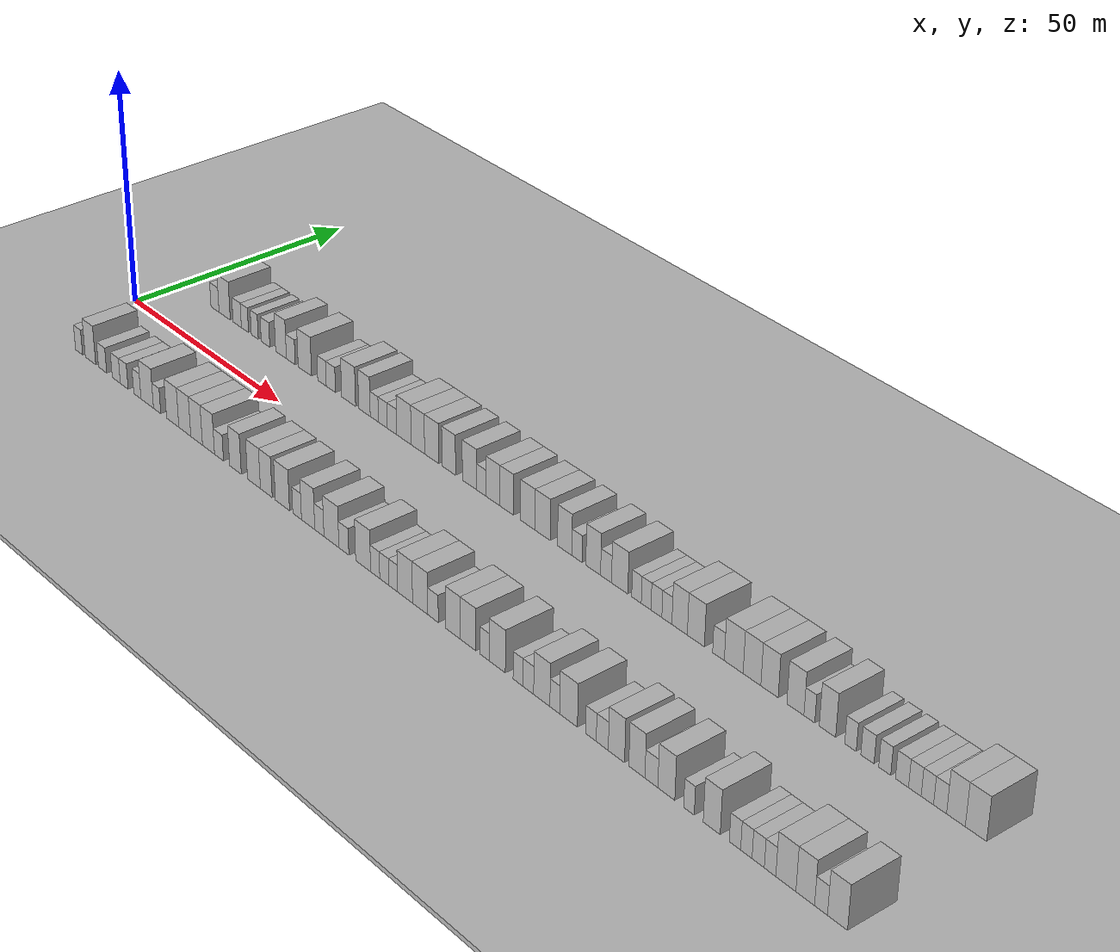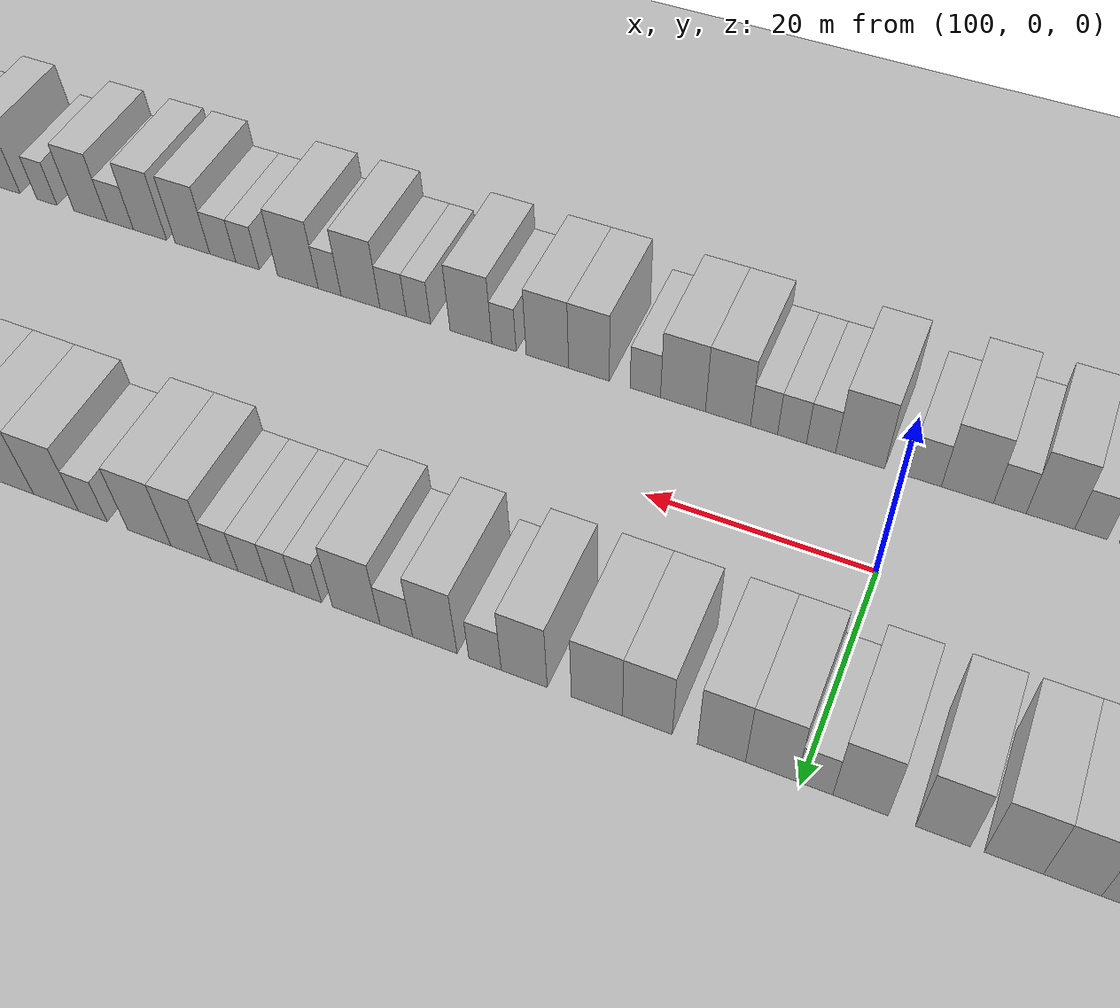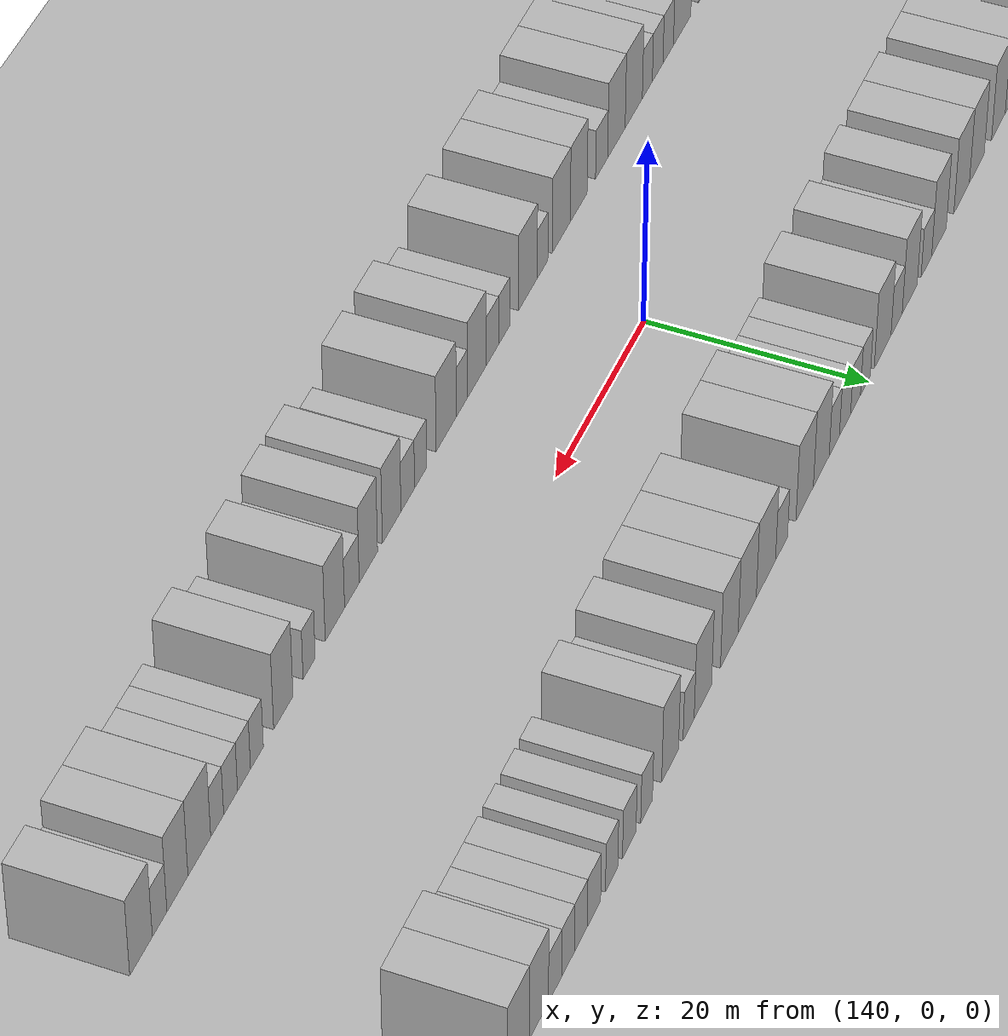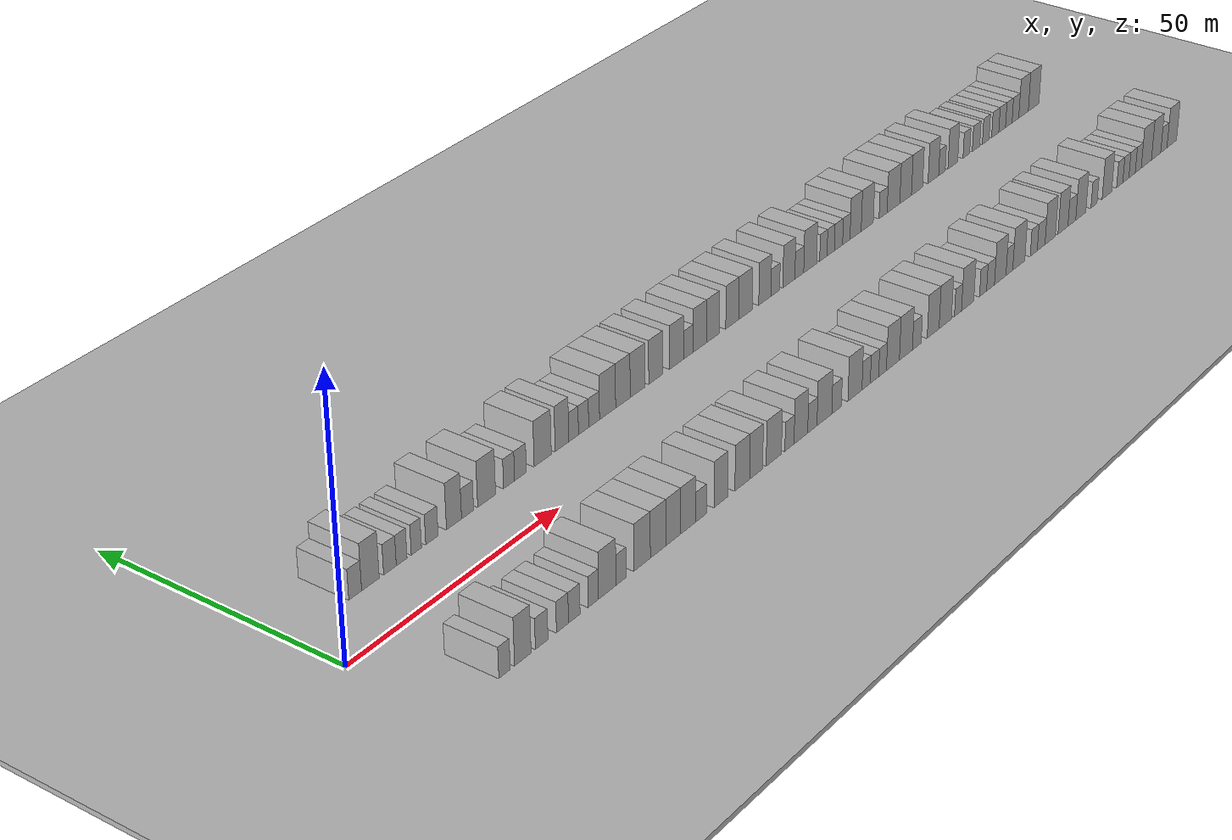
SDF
<?xml version="1.0" encoding="utf-8"?>

<sdf version="1.6">

   <world name="default">

      <gui fullscreen="0">

         <camera name="user_camera">

            <pose>-15 0 4.57585 0 0 0</pose>

            <view_controller>orbit</view_controller>

         </camera>

      </gui>

      <scene>

         <sky>

           <clouds>

             <speed>12</speed>

           </clouds>

         </sky>

         <ambient>0.4 0.4 0.4 1</ambient>

         <background>0.7 0.7 0.7 1</background>

         <shadows>1</shadows>

      </scene>

      <gravity>0 0 -9.8066</gravity>

      <magnetic_field>6e-06 2.3e-05 -4.2e-05</magnetic_field>

      <physics default="0" name="default_physics" type="ode">

         <ode>

            <solver>

               <type>quick</type>

               <iters>10</iters>

               <sor>1.0</sor>

               <use_dynamic_moi_rescaling>0</use_dynamic_moi_rescaling>

            </solver>

            <constraints>

               <cfm>0</cfm>

               <erp>0.2</erp>

               <contact_max_correcting_vel>100</contact_max_correcting_vel>

               <contact_surface_layer>0.001</contact_surface_layer>

            </constraints>

         </ode>

         <max_step_size>0.004</max_step_size>

         <real_time_factor>1</real_time_factor>

         <real_time_update_rate>250</real_time_update_rate>

      </physics>

      <light name="sun" type="directional">

         <cast_shadows>1</cast_shadows>

         <pose>0 0 10 0 0 0</pose>

         <diffuse>0.8 0.8 0.8 1</diffuse>

         <specular>0.2 0.2 0.2 1</specular>

         <attenuation>

            <range>1000</range>

            <constant>0.9</constant>

            <linear>0.01</linear>

            <quadratic>0.001</quadratic>

         </attenuation>

         <direction>-0.5 0.1 -0.9</direction>

      </light>

      <include>

         <name>ground_plane_1</name>

         <uri>model://HANNAS_ground_plane</uri>

         <pose>0 0 0  0 0 0</pose>

      </include>

      <include>

         <name>ground_plane_2</name>

         <uri>model://HANNAS_ground_plane</uri>

         <pose>100 0 0  0 0 0</pose>

      </include>

      <model name="building_1">

         <static>1</static>

         <pose frame="">13.4440 15.0000 0 0.000000 0.000000 1.570796</pose>

         <link name="link">

            <pose frame="">0 0 3.00 0 0 0</pose>

            <collision name="collision">

               <geometry>

                  <box>

                     <size>10.0000 2.8879 6.0000</size>

                  </box>

               </geometry>

               <max_contacts>10</max_contacts>

               <surface>

                  <contact>

                     <ode/>

                  </contact>

                  <bounce/>

                  <friction>

                     <torsional>

                        <ode/>

                     </torsional>

                     <ode/>

                  </friction>

               </surface>

            </collision>

            <visual name="visual">

               <cast_shadows>0</cast_shadows>

               <geometry>

                  <box>

                     <size>10.0000 2.8879 6.0000</size>

                  </box>

               </geometry>

               <material>

                  <script>

                     <uri>model://HANNAS_wall/materials/scripts</uri>

                     <uri>model://HANNAS_wall/materials/textures</uri>

                     <name>vrc/HANNAS_wall</name>

                  </script>

               </material>

            </visual>

            <self_collide>0</self_collide>

            <enable_wind>0</enable_wind>

            <kinematic>0</kinematic>

         </link>

      </model>

      <model name="building_2">

         <static>1</static>

         <pose frame="">16.8819 15.0000 0 0.000000 0.000000 1.570796</pose>

         <link name="link">

            <pose frame="">0 0 4.50 0 0 0</pose>

            <collision name="collision">

               <geometry>

                  <box>

                     <size>10.0000 3.9879 9.0000</size>

                  </box>

               </geometry>

               <max_contacts>10</max_contacts>

               <surface>

                  <contact>

                     <ode/>

                  </contact>

                  <bounce/>

                  <friction>

                     <torsional>

                        <ode/>

                     </torsional>

                     <ode/>

                  </friction>

               </surface>

            </collision>

            <visual name="visual">

               <cast_shadows>0</cast_shadows>

               <geometry>

                  <box>

                     <size>10.0000 3.9879 9.0000</size>

                  </box>

               </geometry>

               <material>

                  <script>

                     <uri>model://HANNAS_wall/materials/scripts</uri>

                     <uri>model://HANNAS_wall/materials/textures</uri>

                     <name>vrc/HANNAS_wall</name>

                  </script>

               </material>

            </visual>

            <self_collide>0</self_collide>

            <enable_wind>0</enable_wind>

            <kinematic>0</kinematic>

         </link>

      </model>

      <model name="building_3">

         <static>1</static>

         <pose frame="">21.3329 15.0000 0 0.000000 0.000000 1.570796</pose>

         <link name="link">

            <pose frame="">0 0 3.00 0 0 0</pose>

            <collision name="collision">

               <geometry>

                  <box>

                     <size>10.0000 2.9140 6.0000</size>

                  </box>

               </geometry>

               <max_contacts>10</max_contacts>

               <surface>

                  <contact>

                     <ode/>

                  </contact>

                  <bounce/>

                  <friction>

                     <torsional>

                        <ode/>

                     </torsional>

                     <ode/>

                  </friction>

               </surface>

            </collision>

            <visual name="visual">

               <cast_shadows>0</cast_shadows>

               <geometry>

                  <box>

                     <size>10.0000 2.9140 6.0000</size>

                  </box>

               </geometry>

               <material>

                  <script>

                     <uri>model://HANNAS_wall/materials/scripts</uri>

                     <uri>model://HANNAS_wall/materials/textures</uri>

                     <name>vrc/HANNAS_wall</name>

                  </script>

               </material>

            </visual>

            <self_collide>0</self_collide>

            <enable_wind>0</enable_wind>

            <kinematic>0</kinematic>

         </link>

      </model>

      <model name="building_4">

         <static>1</static>

         <pose frame="">24.0286 15.0000 0 0.000000 0.000000 1.570796</pose>

         <link name="link">

            <pose frame="">0 0 3.00 0 0 0</pose>

            <collision name="collision">

               <geometry>

                  <box>

                     <size>10.0000 2.4774 6.0000</size>

                  </box>

               </geometry>

               <max_contacts>10</max_contacts>

               <surface>

                  <contact>

                     <ode/>

                  </contact>

                  <bounce/>

                  <friction>

                     <torsional>

                        <ode/>

                     </torsional>

                     <ode/>

                  </friction>

               </surface>

            </collision>

            <visual name="visual">

               <cast_shadows>0</cast_shadows>

               <geometry>

                  <box>

                     <size>10.0000 2.4774 6.0000</size>

                  </box>

               </geometry>

               <material>

                  <script>

                     <uri>model://HANNAS_wall/materials/scripts</uri>

                     <uri>model://HANNAS_wall/materials/textures</uri>

                     <name>vrc/HANNAS_wall</name>

                  </script>

               </material>

            </visual>

            <self_collide>0</self_collide>

            <enable_wind>0</enable_wind>

            <kinematic>0</kinematic>

         </link>

      </model>

      <model name="building_5">

         <static>1</static>

         <pose frame="">27.4679 15.0000 0 0.000000 0.000000 1.570796</pose>

         <link name="link">

            <pose frame="">0 0 3.00 0 0 0</pose>

            <collision name="collision">

               <geometry>

                  <box>

                     <size>10.0000 2.4012 6.0000</size>

                  </box>

               </geometry>

               <max_contacts>10</max_contacts>

               <surface>

                  <contact>

                     <ode/>

                  </contact>

                  <bounce/>

                  <friction>

                     <torsional>

                        <ode/>

                     </torsional>

                     <ode/>

                  </friction>

               </surface>

            </collision>

            <visual name="visual">

               <cast_shadows>0</cast_shadows>

               <geometry>

                  <box>

                     <size>10.0000 2.4012 6.0000</size>

                  </box>

               </geometry>

               <material>

                  <script>

                     <uri>model://HANNAS_wall/materials/scripts</uri>

                     <uri>model://HANNAS_wall/materials/textures</uri>

                     <name>vrc/HANNAS_wall</name>

                  </script>

               </material>

            </visual>

            <self_collide>0</self_collide>

            <enable_wind>0</enable_wind>

            <kinematic>0</kinematic>

         </link>

      </model>

      <model name="building_6">

         <static>1</static>

         <pose frame="">31.1410 15.0000 0 0.000000 0.000000 1.570796</pose>

         <link name="link">

            <pose frame="">0 0 3.00 0 0 0</pose>

            <collision name="collision">

               <geometry>

                  <box>

                     <size>10.0000 2.9450 6.0000</size>

                  </box>

               </geometry>

               <max_contacts>10</max_contacts>

               <surface>

                  <contact>

                     <ode/>

                  </contact>

                  <bounce/>

                  <friction>

                     <torsional>

                        <ode/>

                     </torsional>

                     <ode/>

                  </friction>

               </surface>

            </collision>

            <visual name="visual">

               <cast_shadows>0</cast_shadows>

               <geometry>

                  <box>

                     <size>10.0000 2.9450 6.0000</size>

                  </box>

               </geometry>

               <material>

                  <script>

                     <uri>model://HANNAS_wall/materials/scripts</uri>

                     <uri>model://HANNAS_wall/materials/textures</uri>

                     <name>vrc/HANNAS_wall</name>

                  </script>

               </material>

            </visual>

            <self_collide>0</self_collide>

            <enable_wind>0</enable_wind>

            <kinematic>0</kinematic>

         </link>

      </model>

      <model name="building_7">

         <static>1</static>

         <pose frame="">36.4370 15.0000 0 0.000000 0.000000 1.570796</pose>

         <link name="link">

            <pose frame="">0 0 4.50 0 0 0</pose>

            <collision name="collision">

               <geometry>

                  <box>

                     <size>10.0000 3.6470 9.0000</size>

                  </box>

               </geometry>

               <max_contacts>10</max_contacts>

               <surface>

                  <contact>

                     <ode/>

                  </contact>

                  <bounce/>

                  <friction>

                     <torsional>

                        <ode/>

                     </torsional>

                     <ode/>

                  </friction>

               </surface>

            </collision>

            <visual name="visual">

               <cast_shadows>0</cast_shadows>

               <geometry>

                  <box>

                     <size>10.0000 3.6470 9.0000</size>

                  </box>

               </geometry>

               <material>

                  <script>

                     <uri>model://HANNAS_wall/materials/scripts</uri>

                     <uri>model://HANNAS_wall/materials/textures</uri>

                     <name>vrc/HANNAS_wall</name>

                  </script>

               </material>

            </visual>

            <self_collide>0</self_collide>

            <enable_wind>0</enable_wind>

            <kinematic>0</kinematic>

         </link>

      </model>

      <model name="building_8">

         <static>1</static>

         <pose frame="">39.7335 15.0000 0 0.000000 0.000000 1.570796</pose>

         <link name="link">

            <pose frame="">0 0 3.00 0 0 0</pose>

            <collision name="collision">

               <geometry>

                  <box>

                     <size>10.0000 2.9459 6.0000</size>

                  </box>

               </geometry>

               <max_contacts>10</max_contacts>

               <surface>

                  <contact>

                     <ode/>

                  </contact>

                  <bounce/>

                  <friction>

                     <torsional>

                        <ode/>

                     </torsional>

                     <ode/>

                  </friction>

               </surface>

            </collision>

            <visual name="visual">

               <cast_shadows>0</cast_shadows>

               <geometry>

                  <box>

                     <size>10.0000 2.9459 6.0000</size>

                  </box>

               </geometry>

               <material>

                  <script>

                     <uri>model://HANNAS_wall/materials/scripts</uri>

                     <uri>model://HANNAS_wall/materials/textures</uri>

                     <name>vrc/HANNAS_wall</name>

                  </script>

               </material>

            </visual>

            <self_collide>0</self_collide>

            <enable_wind>0</enable_wind>

            <kinematic>0</kinematic>

         </link>

      </model>

      <model name="building_9">

         <static>1</static>

         <pose frame="">44.4339 15.0000 0 0.000000 0.000000 1.570796</pose>

         <link name="link">

            <pose frame="">0 0 4.50 0 0 0</pose>

            <collision name="collision">

               <geometry>

                  <box>

                     <size>10.0000 4.4549 9.0000</size>

                  </box>

               </geometry>

               <max_contacts>10</max_contacts>

               <surface>

                  <contact>

                     <ode/>

                  </contact>

                  <bounce/>

                  <friction>

                     <torsional>

                        <ode/>

                     </torsional>

                     <ode/>

                  </friction>

               </surface>

            </collision>

            <visual name="visual">

               <cast_shadows>0</cast_shadows>

               <geometry>

                  <box>

                     <size>10.0000 4.4549 9.0000</size>

                  </box>

               </geometry>

               <material>

                  <script>

                     <uri>model://HANNAS_wall/materials/scripts</uri>

                     <uri>model://HANNAS_wall/materials/textures</uri>

                     <name>vrc/HANNAS_wall</name>

                  </script>

               </material>

            </visual>

            <self_collide>0</self_collide>

            <enable_wind>0</enable_wind>

            <kinematic>0</kinematic>

         </link>

      </model>

      <model name="building_10">

         <static>1</static>

         <pose frame="">50.0576 15.0000 0 0.000000 0.000000 1.570796</pose>

         <link name="link">

            <pose frame="">0 0 3.00 0 0 0</pose>

            <collision name="collision">

               <geometry>

                  <box>

                     <size>10.0000 2.7924 6.0000</size>

                  </box>

               </geometry>

               <max_contacts>10</max_contacts>

               <surface>

                  <contact>

                     <ode/>

                  </contact>

                  <bounce/>

                  <friction>

                     <torsional>

                        <ode/>

                     </torsional>

                     <ode/>

                  </friction>

               </surface>

            </collision>

            <visual name="visual">

               <cast_shadows>0</cast_shadows>

               <geometry>

                  <box>

                     <size>10.0000 2.7924 6.0000</size>

                  </box>

               </geometry>

               <material>

                  <script>

                     <uri>model://HANNAS_wall/materials/scripts</uri>

                     <uri>model://HANNAS_wall/materials/textures</uri>

                     <name>vrc/HANNAS_wall</name>

                  </script>

               </material>

            </visual>

            <self_collide>0</self_collide>

            <enable_wind>0</enable_wind>

            <kinematic>0</kinematic>

         </link>

      </model>

      <model name="building_11">

         <static>1</static>

         <pose frame="">52.9522 15.0000 0 0.000000 0.000000 1.570796</pose>

         <link name="link">

            <pose frame="">0 0 3.00 0 0 0</pose>

            <collision name="collision">

               <geometry>

                  <box>

                     <size>10.0000 2.9969 6.0000</size>

                  </box>

               </geometry>

               <max_contacts>10</max_contacts>

               <surface>

                  <contact>

                     <ode/>

                  </contact>

                  <bounce/>

                  <friction>

                     <torsional>

                        <ode/>

                     </torsional>

                     <ode/>

                  </friction>

               </surface>

            </collision>

            <visual name="visual">

               <cast_shadows>0</cast_shadows>

               <geometry>

                  <box>

                     <size>10.0000 2.9969 6.0000</size>

                  </box>

               </geometry>

               <material>

                  <script>

                     <uri>model://HANNAS_wall/materials/scripts</uri>

                     <uri>model://HANNAS_wall/materials/textures</uri>

                     <name>vrc/HANNAS_wall</name>

                  </script>

               </material>

            </visual>

            <self_collide>0</self_collide>

            <enable_wind>0</enable_wind>

            <kinematic>0</kinematic>

         </link>

      </model>

      <model name="building_12">

         <static>1</static>

         <pose frame="">58.6778 15.0000 0 0.000000 0.000000 1.570796</pose>

         <link name="link">

            <pose frame="">0 0 4.50 0 0 0</pose>

            <collision name="collision">

               <geometry>

                  <box>

                     <size>10.0000 4.4542 9.0000</size>

                  </box>

               </geometry>

               <max_contacts>10</max_contacts>

               <surface>

                  <contact>

                     <ode/>

                  </contact>

                  <bounce/>

                  <friction>

                     <torsional>

                        <ode/>

                     </torsional>

                     <ode/>

                  </friction>

               </surface>

            </collision>

            <visual name="visual">

               <cast_shadows>0</cast_shadows>

               <geometry>

                  <box>

                     <size>10.0000 4.4542 9.0000</size>

                  </box>

               </geometry>

               <material>

                  <script>

                     <uri>model://HANNAS_wall/materials/scripts</uri>

                     <uri>model://HANNAS_wall/materials/textures</uri>

                     <name>vrc/HANNAS_wall</name>

                  </script>

               </material>

            </visual>

            <self_collide>0</self_collide>

            <enable_wind>0</enable_wind>

            <kinematic>0</kinematic>

         </link>

      </model>

      <model name="building_13">

         <static>1</static>

         <pose frame="">63.7187 15.0000 0 0.000000 0.000000 1.570796</pose>

         <link name="link">

            <pose frame="">0 0 4.50 0 0 0</pose>

            <collision name="collision">

               <geometry>

                  <box>

                     <size>10.0000 3.6277 9.0000</size>

                  </box>

               </geometry>

               <max_contacts>10</max_contacts>

               <surface>

                  <contact>

                     <ode/>

                  </contact>

                  <bounce/>

                  <friction>

                     <torsional>

                        <ode/>

                     </torsional>

                     <ode/>

                  </friction>

               </surface>

            </collision>

            <visual name="visual">

               <cast_shadows>0</cast_shadows>

               <geometry>

                  <box>

                     <size>10.0000 3.6277 9.0000</size>

                  </box>

               </geometry>

               <material>

                  <script>

                     <uri>model://HANNAS_wall/materials/scripts</uri>

                     <uri>model://HANNAS_wall/materials/textures</uri>

                     <name>vrc/HANNAS_wall</name>

                  </script>

               </material>

            </visual>

            <self_collide>0</self_collide>

            <enable_wind>0</enable_wind>

            <kinematic>0</kinematic>

         </link>

      </model>

      <model name="building_14">

         <static>1</static>

         <pose frame="">66.8152 15.0000 0 0.000000 0.000000 1.570796</pose>

         <link name="link">

            <pose frame="">0 0 3.00 0 0 0</pose>

            <collision name="collision">

               <geometry>

                  <box>

                     <size>10.0000 2.5653 6.0000</size>

                  </box>

               </geometry>

               <max_contacts>10</max_contacts>

               <surface>

                  <contact>

                     <ode/>

                  </contact>

                  <bounce/>

                  <friction>

                     <torsional>

                        <ode/>

                     </torsional>

                     <ode/>

                  </friction>

               </surface>

            </collision>

            <visual name="visual">

               <cast_shadows>0</cast_shadows>

               <geometry>

                  <box>

                     <size>10.0000 2.5653 6.0000</size>

                  </box>

               </geometry>

               <material>

                  <script>

                     <uri>model://HANNAS_wall/materials/scripts</uri>

                     <uri>model://HANNAS_wall/materials/textures</uri>

                     <name>vrc/HANNAS_wall</name>

                  </script>

               </material>

            </visual>

            <self_collide>0</self_collide>

            <enable_wind>0</enable_wind>

            <kinematic>0</kinematic>

         </link>

      </model>

      <model name="building_15">

         <static>1</static>

         <pose frame="">69.4661 15.0000 0 0.000000 0.000000 1.570796</pose>

         <link name="link">

            <pose frame="">0 0 3.00 0 0 0</pose>

            <collision name="collision">

               <geometry>

                  <box>

                     <size>10.0000 2.7366 6.0000</size>

                  </box>

               </geometry>

               <max_contacts>10</max_contacts>

               <surface>

                  <contact>

                     <ode/>

                  </contact>

                  <bounce/>

                  <friction>

                     <torsional>

                        <ode/>

                     </torsional>

                     <ode/>

                  </friction>

               </surface>

            </collision>

            <visual name="visual">

               <cast_shadows>0</cast_shadows>

               <geometry>

                  <box>

                     <size>10.0000 2.7366 6.0000</size>

                  </box>

               </geometry>

               <material>

                  <script>

                     <uri>model://HANNAS_wall/materials/scripts</uri>

                     <uri>model://HANNAS_wall/materials/textures</uri>

                     <name>vrc/HANNAS_wall</name>

                  </script>

               </material>

            </visual>

            <self_collide>0</self_collide>

            <enable_wind>0</enable_wind>

            <kinematic>0</kinematic>

         </link>

      </model>

      <model name="building_16">

         <static>1</static>

         <pose frame="">72.3064 15.0000 0 0.000000 0.000000 1.570796</pose>

         <link name="link">

            <pose frame="">0 0 3.00 0 0 0</pose>

            <collision name="collision">

               <geometry>

                  <box>

                     <size>10.0000 2.9440 6.0000</size>

                  </box>

               </geometry>

               <max_contacts>10</max_contacts>

               <surface>

                  <contact>

                     <ode/>

                  </contact>

                  <bounce/>

                  <friction>

                     <torsional>

                        <ode/>

                     </torsional>

                     <ode/>

                  </friction>

               </surface>

            </collision>

            <visual name="visual">

               <cast_shadows>0</cast_shadows>

               <geometry>

                  <box>

                     <size>10.0000 2.9440 6.0000</size>

                  </box>

               </geometry>

               <material>

                  <script>

                     <uri>model://HANNAS_wall/materials/scripts</uri>

                     <uri>model://HANNAS_wall/materials/textures</uri>

                     <name>vrc/HANNAS_wall</name>

                  </script>

               </material>

            </visual>

            <self_collide>0</self_collide>

            <enable_wind>0</enable_wind>

            <kinematic>0</kinematic>

         </link>

      </model>

      <model name="building_17">

         <static>1</static>

         <pose frame="">75.9872 15.0000 0 0.000000 0.000000 1.570796</pose>

         <link name="link">

            <pose frame="">0 0 4.50 0 0 0</pose>

            <collision name="collision">

               <geometry>

                  <box>

                     <size>10.0000 4.4175 9.0000</size>

                  </box>

               </geometry>

               <max_contacts>10</max_contacts>

               <surface>

                  <contact>

                     <ode/>

                  </contact>

                  <bounce/>

                  <friction>

                     <torsional>

                        <ode/>

                     </torsional>

                     <ode/>

                  </friction>

               </surface>

            </collision>

            <visual name="visual">

               <cast_shadows>0</cast_shadows>

               <geometry>

                  <box>

                     <size>10.0000 4.4175 9.0000</size>

                  </box>

               </geometry>

               <material>

                  <script>

                     <uri>model://HANNAS_wall/materials/scripts</uri>

                     <uri>model://HANNAS_wall/materials/textures</uri>

                     <name>vrc/HANNAS_wall</name>

                  </script>

               </material>

            </visual>

            <self_collide>0</self_collide>

            <enable_wind>0</enable_wind>

            <kinematic>0</kinematic>

         </link>

      </model>

      <model name="building_18">

         <static>1</static>

         <pose frame="">80.2217 15.0000 0 0.000000 0.000000 1.570796</pose>

         <link name="link">

            <pose frame="">0 0 4.50 0 0 0</pose>

            <collision name="collision">

               <geometry>

                  <box>

                     <size>10.0000 4.0515 9.0000</size>

                  </box>

               </geometry>

               <max_contacts>10</max_contacts>

               <surface>

                  <contact>

                     <ode/>

                  </contact>

                  <bounce/>

                  <friction>

                     <torsional>

                        <ode/>

                     </torsional>

                     <ode/>

                  </friction>

               </surface>

            </collision>

            <visual name="visual">

               <cast_shadows>0</cast_shadows>

               <geometry>

                  <box>

                     <size>10.0000 4.0515 9.0000</size>

                  </box>

               </geometry>

               <material>

                  <script>

                     <uri>model://HANNAS_wall/materials/scripts</uri>

                     <uri>model://HANNAS_wall/materials/textures</uri>

                     <name>vrc/HANNAS_wall</name>

                  </script>

               </material>

            </visual>

            <self_collide>0</self_collide>

            <enable_wind>0</enable_wind>

            <kinematic>0</kinematic>

         </link>

      </model>

      <model name="building_19">

         <static>1</static>

         <pose frame="">84.3455 15.0000 0 0.000000 0.000000 1.570796</pose>

         <link name="link">

            <pose frame="">0 0 4.50 0 0 0</pose>

            <collision name="collision">

               <geometry>

                  <box>

                     <size>10.0000 4.1960 9.0000</size>

                  </box>

               </geometry>

               <max_contacts>10</max_contacts>

               <surface>

                  <contact>

                     <ode/>

                  </contact>

                  <bounce/>

                  <friction>

                     <torsional>

                        <ode/>

                     </torsional>

                     <ode/>

                  </friction>

               </surface>

            </collision>

            <visual name="visual">

               <cast_shadows>0</cast_shadows>

               <geometry>

                  <box>

                     <size>10.0000 4.1960 9.0000</size>

                  </box>

               </geometry>

               <material>

                  <script>

                     <uri>model://HANNAS_wall/materials/scripts</uri>

                     <uri>model://HANNAS_wall/materials/textures</uri>

                     <name>vrc/HANNAS_wall</name>

                  </script>

               </material>

            </visual>

            <self_collide>0</self_collide>

            <enable_wind>0</enable_wind>

            <kinematic>0</kinematic>

         </link>

      </model>

      <model name="building_20">

         <static>1</static>

         <pose frame="">89.4434 15.0000 0 0.000000 0.000000 1.570796</pose>

         <link name="link">

            <pose frame="">0 0 4.50 0 0 0</pose>

            <collision name="collision">

               <geometry>

                  <box>

                     <size>10.0000 4.0000 9.0000</size>

                  </box>

               </geometry>

               <max_contacts>10</max_contacts>

               <surface>

                  <contact>

                     <ode/>

                  </contact>

                  <bounce/>

                  <friction>

                     <torsional>

                        <ode/>

                     </torsional>

                     <ode/>

                  </friction>

               </surface>

            </collision>

            <visual name="visual">

               <cast_shadows>0</cast_shadows>

               <geometry>

                  <box>

                     <size>10.0000 4.0000 9.0000</size>

                  </box>

               </geometry>

               <material>

                  <script>

                     <uri>model://HANNAS_wall/materials/scripts</uri>

                     <uri>model://HANNAS_wall/materials/textures</uri>

                     <name>vrc/HANNAS_wall</name>

                  </script>

               </material>

            </visual>

            <self_collide>0</self_collide>

            <enable_wind>0</enable_wind>

            <kinematic>0</kinematic>

         </link>

      </model>

      <model name="building_21">

         <static>1</static>

         <pose frame="">95.5154 15.0000 0 0.000000 0.000000 1.570796</pose>

         <link name="link">

            <pose frame="">0 0 4.50 0 0 0</pose>

            <collision name="collision">

               <geometry>

                  <box>

                     <size>10.0000 4.1440 9.0000</size>

                  </box>

               </geometry>

               <max_contacts>10</max_contacts>

               <surface>

                  <contact>

                     <ode/>

                  </contact>

                  <bounce/>

                  <friction>

                     <torsional>

                        <ode/>

                     </torsional>

                     <ode/>

                  </friction>

               </surface>

            </collision>

            <visual name="visual">

               <cast_shadows>0</cast_shadows>

               <geometry>

                  <box>

                     <size>10.0000 4.1440 9.0000</size>

                  </box>

               </geometry>

               <material>

                  <script>

                     <uri>model://HANNAS_wall/materials/scripts</uri>

                     <uri>model://HANNAS_wall/materials/textures</uri>

                     <name>vrc/HANNAS_wall</name>

                  </script>

               </material>

            </visual>

            <self_collide>0</self_collide>

            <enable_wind>0</enable_wind>

            <kinematic>0</kinematic>

         </link>

      </model>

      <model name="building_22">

         <static>1</static>

         <pose frame="">98.9690 15.0000 0 0.000000 0.000000 1.570796</pose>

         <link name="link">

            <pose frame="">0 0 3.00 0 0 0</pose>

            <collision name="collision">

               <geometry>

                  <box>

                     <size>10.0000 2.7631 6.0000</size>

                  </box>

               </geometry>

               <max_contacts>10</max_contacts>

               <surface>

                  <contact>

                     <ode/>

                  </contact>

                  <bounce/>

                  <friction>

                     <torsional>

                        <ode/>

                     </torsional>

                     <ode/>

                  </friction>

               </surface>

            </collision>

            <visual name="visual">

               <cast_shadows>0</cast_shadows>

               <geometry>

                  <box>

                     <size>10.0000 2.7631 6.0000</size>

                  </box>

               </geometry>

               <material>

                  <script>

                     <uri>model://HANNAS_wall/materials/scripts</uri>

                     <uri>model://HANNAS_wall/materials/textures</uri>

                     <name>vrc/HANNAS_wall</name>

                  </script>

               </material>

            </visual>

            <self_collide>0</self_collide>

            <enable_wind>0</enable_wind>

            <kinematic>0</kinematic>

         </link>

      </model>

      <model name="building_23">

         <static>1</static>

         <pose frame="">102.3103 15.0000 0 0.000000 0.000000 1.570796</pose>

         <link name="link">

            <pose frame="">0 0 4.50 0 0 0</pose>

            <collision name="collision">

               <geometry>

                  <box>

                     <size>10.0000 3.9195 9.0000</size>

                  </box>

               </geometry>

               <max_contacts>10</max_contacts>

               <surface>

                  <contact>

                     <ode/>

                  </contact>

                  <bounce/>

                  <friction>

                     <torsional>

                        <ode/>

                     </torsional>

                     <ode/>

                  </friction>

               </surface>

            </collision>

            <visual name="visual">

               <cast_shadows>0</cast_shadows>

               <geometry>

                  <box>

                     <size>10.0000 3.9195 9.0000</size>

                  </box>

               </geometry>

               <material>

                  <script>

                     <uri>model://HANNAS_wall/materials/scripts</uri>

                     <uri>model://HANNAS_wall/materials/textures</uri>

                     <name>vrc/HANNAS_wall</name>

                  </script>

               </material>

            </visual>

            <self_collide>0</self_collide>

            <enable_wind>0</enable_wind>

            <kinematic>0</kinematic>

         </link>

      </model>

      <model name="building_24">

         <static>1</static>

         <pose frame="">106.1572 15.0000 0 0.000000 0.000000 1.570796</pose>

         <link name="link">

            <pose frame="">0 0 4.50 0 0 0</pose>

            <collision name="collision">

               <geometry>

                  <box>

                     <size>10.0000 3.7744 9.0000</size>

                  </box>

               </geometry>

               <max_contacts>10</max_contacts>

               <surface>

                  <contact>

                     <ode/>

                  </contact>

                  <bounce/>

                  <friction>

                     <torsional>

                        <ode/>

                     </torsional>

                     <ode/>

                  </friction>

               </surface>

            </collision>

            <visual name="visual">

               <cast_shadows>0</cast_shadows>

               <geometry>

                  <box>

                     <size>10.0000 3.7744 9.0000</size>

                  </box>

               </geometry>

               <material>

                  <script>

                     <uri>model://HANNAS_wall/materials/scripts</uri>

                     <uri>model://HANNAS_wall/materials/textures</uri>

                     <name>vrc/HANNAS_wall</name>

                  </script>

               </material>

            </visual>

            <self_collide>0</self_collide>

            <enable_wind>0</enable_wind>

            <kinematic>0</kinematic>

         </link>

      </model>

      <model name="building_25">

         <static>1</static>

         <pose frame="">112.0413 15.0000 0 0.000000 0.000000 1.570796</pose>

         <link name="link">

            <pose frame="">0 0 4.50 0 0 0</pose>

            <collision name="collision">

               <geometry>

                  <box>

                     <size>10.0000 3.9937 9.0000</size>

                  </box>

               </geometry>

               <max_contacts>10</max_contacts>

               <surface>

                  <contact>

                     <ode/>

                  </contact>

                  <bounce/>

                  <friction>

                     <torsional>

                        <ode/>

                     </torsional>

                     <ode/>

                  </friction>

               </surface>

            </collision>

            <visual name="visual">

               <cast_shadows>0</cast_shadows>

               <geometry>

                  <box>

                     <size>10.0000 3.9937 9.0000</size>

                  </box>

               </geometry>

               <material>

                  <script>

                     <uri>model://HANNAS_wall/materials/scripts</uri>

                     <uri>model://HANNAS_wall/materials/textures</uri>

                     <name>vrc/HANNAS_wall</name>

                  </script>

               </material>

            </visual>

            <self_collide>0</self_collide>

            <enable_wind>0</enable_wind>

            <kinematic>0</kinematic>

         </link>

      </model>

      <model name="building_26">

         <static>1</static>

         <pose frame="">116.1255 15.0000 0 0.000000 0.000000 1.570796</pose>

         <link name="link">

            <pose frame="">0 0 4.50 0 0 0</pose>

            <collision name="collision">

               <geometry>

                  <box>

                     <size>10.0000 4.1748 9.0000</size>

                  </box>

               </geometry>

               <max_contacts>10</max_contacts>

               <surface>

                  <contact>

                     <ode/>

                  </contact>

                  <bounce/>

                  <friction>

                     <torsional>

                        <ode/>

                     </torsional>

                     <ode/>

                  </friction>

               </surface>

            </collision>

            <visual name="visual">

               <cast_shadows>0</cast_shadows>

               <geometry>

                  <box>

                     <size>10.0000 4.1748 9.0000</size>

                  </box>

               </geometry>

               <material>

                  <script>

                     <uri>model://HANNAS_wall/materials/scripts</uri>

                     <uri>model://HANNAS_wall/materials/textures</uri>

                     <name>vrc/HANNAS_wall</name>

                  </script>

               </material>

            </visual>

            <self_collide>0</self_collide>

            <enable_wind>0</enable_wind>

            <kinematic>0</kinematic>

         </link>

      </model>

      <model name="building_27">

         <static>1</static>

         <pose frame="">122.1426 15.0000 0 0.000000 0.000000 1.570796</pose>

         <link name="link">

            <pose frame="">0 0 4.50 0 0 0</pose>

            <collision name="collision">

               <geometry>

                  <box>

                     <size>10.0000 3.8595 9.0000</size>

                  </box>

               </geometry>

               <max_contacts>10</max_contacts>

               <surface>

                  <contact>

                     <ode/>

                  </contact>

                  <bounce/>

                  <friction>

                     <torsional>

                        <ode/>

                     </torsional>

                     <ode/>

                  </friction>

               </surface>

            </collision>

            <visual name="visual">

               <cast_shadows>0</cast_shadows>

               <geometry>

                  <box>

                     <size>10.0000 3.8595 9.0000</size>

                  </box>

               </geometry>

               <material>

                  <script>

                     <uri>model://HANNAS_wall/materials/scripts</uri>

                     <uri>model://HANNAS_wall/materials/textures</uri>

                     <name>vrc/HANNAS_wall</name>

                  </script>

               </material>

            </visual>

            <self_collide>0</self_collide>

            <enable_wind>0</enable_wind>

            <kinematic>0</kinematic>

         </link>

      </model>

      <model name="building_28">

         <static>1</static>

         <pose frame="">125.4529 15.0000 0 0.000000 0.000000 1.570796</pose>

         <link name="link">

            <pose frame="">0 0 3.00 0 0 0</pose>

            <collision name="collision">

               <geometry>

                  <box>

                     <size>10.0000 2.7610 6.0000</size>

                  </box>

               </geometry>

               <max_contacts>10</max_contacts>

               <surface>

                  <contact>

                     <ode/>

                  </contact>

                  <bounce/>

                  <friction>

                     <torsional>

                        <ode/>

                     </torsional>

                     <ode/>

                  </friction>

               </surface>

            </collision>

            <visual name="visual">

               <cast_shadows>0</cast_shadows>

               <geometry>

                  <box>

                     <size>10.0000 2.7610 6.0000</size>

                  </box>

               </geometry>

               <material>

                  <script>

                     <uri>model://HANNAS_wall/materials/scripts</uri>

                     <uri>model://HANNAS_wall/materials/textures</uri>

                     <name>vrc/HANNAS_wall</name>

                  </script>

               </material>

            </visual>

            <self_collide>0</self_collide>

            <enable_wind>0</enable_wind>

            <kinematic>0</kinematic>

         </link>

      </model>

      <model name="building_29">

         <static>1</static>

         <pose frame="">129.7695 15.0000 0 0.000000 0.000000 1.570796</pose>

         <link name="link">

            <pose frame="">0 0 4.50 0 0 0</pose>

            <collision name="collision">

               <geometry>

                  <box>

                     <size>10.0000 3.8722 9.0000</size>

                  </box>

               </geometry>

               <max_contacts>10</max_contacts>

               <surface>

                  <contact>

                     <ode/>

                  </contact>

                  <bounce/>

                  <friction>

                     <torsional>

                        <ode/>

                     </torsional>

                     <ode/>

                  </friction>

               </surface>

            </collision>

            <visual name="visual">

               <cast_shadows>0</cast_shadows>

               <geometry>

                  <box>

                     <size>10.0000 3.8722 9.0000</size>

                  </box>

               </geometry>

               <material>

                  <script>

                     <uri>model://HANNAS_wall/materials/scripts</uri>

                     <uri>model://HANNAS_wall/materials/textures</uri>

                     <name>vrc/HANNAS_wall</name>

                  </script>

               </material>

            </visual>

            <self_collide>0</self_collide>

            <enable_wind>0</enable_wind>

            <kinematic>0</kinematic>

         </link>

      </model>

      <model name="building_30">

         <static>1</static>

         <pose frame="">133.1367 15.0000 0 0.000000 0.000000 1.570796</pose>

         <link name="link">

            <pose frame="">0 0 3.00 0 0 0</pose>

            <collision name="collision">

               <geometry>

                  <box>

                     <size>10.0000 2.8621 6.0000</size>

                  </box>

               </geometry>

               <max_contacts>10</max_contacts>

               <surface>

                  <contact>

                     <ode/>

                  </contact>

                  <bounce/>

                  <friction>

                     <torsional>

                        <ode/>

                     </torsional>

                     <ode/>

                  </friction>

               </surface>

            </collision>

            <visual name="visual">

               <cast_shadows>0</cast_shadows>

               <geometry>

                  <box>

                     <size>10.0000 2.8621 6.0000</size>

                  </box>

               </geometry>

               <material>

                  <script>

                     <uri>model://HANNAS_wall/materials/scripts</uri>

                     <uri>model://HANNAS_wall/materials/textures</uri>

                     <name>vrc/HANNAS_wall</name>

                  </script>

               </material>

            </visual>

            <self_collide>0</self_collide>

            <enable_wind>0</enable_wind>

            <kinematic>0</kinematic>

         </link>

      </model>

      <model name="building_31">

         <static>1</static>

         <pose frame="">136.6825 15.0000 0 0.000000 0.000000 1.570796</pose>

         <link name="link">

            <pose frame="">0 0 4.50 0 0 0</pose>

            <collision name="collision">

               <geometry>

                  <box>

                     <size>10.0000 4.2296 9.0000</size>

                  </box>

               </geometry>

               <max_contacts>10</max_contacts>

               <surface>

                  <contact>

                     <ode/>

                  </contact>

                  <bounce/>

                  <friction>

                     <torsional>

                        <ode/>

                     </torsional>

                     <ode/>

                  </friction>

               </surface>

            </collision>

            <visual name="visual">

               <cast_shadows>0</cast_shadows>

               <geometry>

                  <box>

                     <size>10.0000 4.2296 9.0000</size>

                  </box>

               </geometry>

               <material>

                  <script>

                     <uri>model://HANNAS_wall/materials/scripts</uri>

                     <uri>model://HANNAS_wall/materials/textures</uri>

                     <name>vrc/HANNAS_wall</name>

                  </script>

               </material>

            </visual>

            <self_collide>0</self_collide>

            <enable_wind>0</enable_wind>

            <kinematic>0</kinematic>

         </link>

      </model>

      <model name="building_32">

         <static>1</static>

         <pose frame="">141.0260 15.0000 0 0.000000 0.000000 1.570796</pose>

         <link name="link">

            <pose frame="">0 0 3.00 0 0 0</pose>

            <collision name="collision">

               <geometry>

                  <box>

                     <size>10.0000 2.4573 6.0000</size>

                  </box>

               </geometry>

               <max_contacts>10</max_contacts>

               <surface>

                  <contact>

                     <ode/>

                  </contact>

                  <bounce/>

                  <friction>

                     <torsional>

                        <ode/>

                     </torsional>

                     <ode/>

                  </friction>

               </surface>

            </collision>

            <visual name="visual">

               <cast_shadows>0</cast_shadows>

               <geometry>

                  <box>

                     <size>10.0000 2.4573 6.0000</size>

                  </box>

               </geometry>

               <material>

                  <script>

                     <uri>model://HANNAS_wall/materials/scripts</uri>

                     <uri>model://HANNAS_wall/materials/textures</uri>

                     <name>vrc/HANNAS_wall</name>

                  </script>

               </material>

            </visual>

            <self_collide>0</self_collide>

            <enable_wind>0</enable_wind>

            <kinematic>0</kinematic>

         </link>

      </model>

      <model name="building_33">

         <static>1</static>

         <pose frame="">143.4801 15.0000 0 0.000000 0.000000 1.570796</pose>

         <link name="link">

            <pose frame="">0 0 3.00 0 0 0</pose>

            <collision name="collision">

               <geometry>

                  <box>

                     <size>10.0000 2.4510 6.0000</size>

                  </box>

               </geometry>

               <max_contacts>10</max_contacts>

               <surface>

                  <contact>

                     <ode/>

                  </contact>

                  <bounce/>

                  <friction>

                     <torsional>

                        <ode/>

                     </torsional>

                     <ode/>

                  </friction>

               </surface>

            </collision>

            <visual name="visual">

               <cast_shadows>0</cast_shadows>

               <geometry>

                  <box>

                     <size>10.0000 2.4510 6.0000</size>

                  </box>

               </geometry>

               <material>

                  <script>

                     <uri>model://HANNAS_wall/materials/scripts</uri>

                     <uri>model://HANNAS_wall/materials/textures</uri>

                     <name>vrc/HANNAS_wall</name>

                  </script>

               </material>

            </visual>

            <self_collide>0</self_collide>

            <enable_wind>0</enable_wind>

            <kinematic>0</kinematic>

         </link>

      </model>

      <model name="building_34">

         <static>1</static>

         <pose frame="">146.0820 15.0000 0 0.000000 0.000000 1.570796</pose>

         <link name="link">

            <pose frame="">0 0 3.00 0 0 0</pose>

            <collision name="collision">

               <geometry>

                  <box>

                     <size>10.0000 2.7527 6.0000</size>

                  </box>

               </geometry>

               <max_contacts>10</max_contacts>

               <surface>

                  <contact>

                     <ode/>

                  </contact>

                  <bounce/>

                  <friction>

                     <torsional>

                        <ode/>

                     </torsional>

                     <ode/>

                  </friction>

               </surface>

            </collision>

            <visual name="visual">

               <cast_shadows>0</cast_shadows>

               <geometry>

                  <box>

                     <size>10.0000 2.7527 6.0000</size>

                  </box>

               </geometry>

               <material>

                  <script>

                     <uri>model://HANNAS_wall/materials/scripts</uri>

                     <uri>model://HANNAS_wall/materials/textures</uri>

                     <name>vrc/HANNAS_wall</name>

                  </script>

               </material>

            </visual>

            <self_collide>0</self_collide>

            <enable_wind>0</enable_wind>

            <kinematic>0</kinematic>

         </link>

      </model>

      <model name="building_35">

         <static>1</static>

         <pose frame="">148.7128 15.0000 0 0.000000 0.000000 1.570796</pose>

         <link name="link">

            <pose frame="">0 0 3.00 0 0 0</pose>

            <collision name="collision">

               <geometry>

                  <box>

                     <size>10.0000 2.5088 6.0000</size>

                  </box>

               </geometry>

               <max_contacts>10</max_contacts>

               <surface>

                  <contact>

                     <ode/>

                  </contact>

                  <bounce/>

                  <friction>

                     <torsional>

                        <ode/>

                     </torsional>

                     <ode/>

                  </friction>

               </surface>

            </collision>

            <visual name="visual">

               <cast_shadows>0</cast_shadows>

               <geometry>

                  <box>

                     <size>10.0000 2.5088 6.0000</size>

                  </box>

               </geometry>

               <material>

                  <script>

                     <uri>model://HANNAS_wall/materials/scripts</uri>

                     <uri>model://HANNAS_wall/materials/textures</uri>

                     <name>vrc/HANNAS_wall</name>

                  </script>

               </material>

            </visual>

            <self_collide>0</self_collide>

            <enable_wind>0</enable_wind>

            <kinematic>0</kinematic>

         </link>

      </model>

      <model name="building_36">

         <static>1</static>

         <pose frame="">151.8779 15.0000 0 0.000000 0.000000 1.570796</pose>

         <link name="link">

            <pose frame="">0 0 4.50 0 0 0</pose>

            <collision name="collision">

               <geometry>

                  <box>

                     <size>10.0000 3.8214 9.0000</size>

                  </box>

               </geometry>

               <max_contacts>10</max_contacts>

               <surface>

                  <contact>

                     <ode/>

                  </contact>

                  <bounce/>

                  <friction>

                     <torsional>

                        <ode/>

                     </torsional>

                     <ode/>

                  </friction>

               </surface>

            </collision>

            <visual name="visual">

               <cast_shadows>0</cast_shadows>

               <geometry>

                  <box>

                     <size>10.0000 3.8214 9.0000</size>

                  </box>

               </geometry>

               <material>

                  <script>

                     <uri>model://HANNAS_wall/materials/scripts</uri>

                     <uri>model://HANNAS_wall/materials/textures</uri>

                     <name>vrc/HANNAS_wall</name>

                  </script>

               </material>

            </visual>

            <self_collide>0</self_collide>

            <enable_wind>0</enable_wind>

            <kinematic>0</kinematic>

         </link>

      </model>

      <model name="building_37">

         <static>1</static>

         <pose frame="">155.8819 15.0000 0 0.000000 0.000000 1.570796</pose>

         <link name="link">

            <pose frame="">0 0 4.50 0 0 0</pose>

            <collision name="collision">

               <geometry>

                  <box>

                     <size>10.0000 4.1867 9.0000</size>

                  </box>

               </geometry>

               <max_contacts>10</max_contacts>

               <surface>

                  <contact>

                     <ode/>

                  </contact>

                  <bounce/>

                  <friction>

                     <torsional>

                        <ode/>

                     </torsional>

                     <ode/>

                  </friction>

               </surface>

            </collision>

            <visual name="visual">

               <cast_shadows>0</cast_shadows>

               <geometry>

                  <box>

                     <size>10.0000 4.1867 9.0000</size>

                  </box>

               </geometry>

               <material>

                  <script>

                     <uri>model://HANNAS_wall/materials/scripts</uri>

                     <uri>model://HANNAS_wall/materials/textures</uri>

                     <name>vrc/HANNAS_wall</name>

                  </script>

               </material>

            </visual>

            <self_collide>0</self_collide>

            <enable_wind>0</enable_wind>

            <kinematic>0</kinematic>

         </link>

      </model>

      <model name="building_38">

         <static>1</static>

         <pose frame="">161.3899 15.0000 0 0.000000 0.000000 1.570796</pose>

         <link name="link">

            <pose frame="">0 0 3.00 0 0 0</pose>

            <collision name="collision">

               <geometry>

                  <box>

                     <size>10.0000 2.8291 6.0000</size>

                  </box>

               </geometry>

               <max_contacts>10</max_contacts>

               <surface>

                  <contact>

                     <ode/>

                  </contact>

                  <bounce/>

                  <friction>

                     <torsional>

                        <ode/>

                     </torsional>

                     <ode/>

                  </friction>

               </surface>

            </collision>

            <visual name="visual">

               <cast_shadows>0</cast_shadows>

               <geometry>

                  <box>

                     <size>10.0000 2.8291 6.0000</size>

                  </box>

               </geometry>

               <material>

                  <script>

                     <uri>model://HANNAS_wall/materials/scripts</uri>

                     <uri>model://HANNAS_wall/materials/textures</uri>

                     <name>vrc/HANNAS_wall</name>

                  </script>

               </material>

            </visual>

            <self_collide>0</self_collide>

            <enable_wind>0</enable_wind>

            <kinematic>0</kinematic>

         </link>

      </model>

      <model name="building_39">

         <static>1</static>

         <pose frame="">165.0470 15.0000 0 0.000000 0.000000 1.570796</pose>

         <link name="link">

            <pose frame="">0 0 4.50 0 0 0</pose>

            <collision name="collision">

               <geometry>

                  <box>

                     <size>10.0000 4.4852 9.0000</size>

                  </box>

               </geometry>

               <max_contacts>10</max_contacts>

               <surface>

                  <contact>

                     <ode/>

                  </contact>

                  <bounce/>

                  <friction>

                     <torsional>

                        <ode/>

                     </torsional>

                     <ode/>

                  </friction>

               </surface>

            </collision>

            <visual name="visual">

               <cast_shadows>0</cast_shadows>

               <geometry>

                  <box>

                     <size>10.0000 4.4852 9.0000</size>

                  </box>

               </geometry>

               <material>

                  <script>

                     <uri>model://HANNAS_wall/materials/scripts</uri>

                     <uri>model://HANNAS_wall/materials/textures</uri>

                     <name>vrc/HANNAS_wall</name>

                  </script>

               </material>

            </visual>

            <self_collide>0</self_collide>

            <enable_wind>0</enable_wind>

            <kinematic>0</kinematic>

         </link>

      </model>

      <model name="building_40">

         <static>1</static>

         <pose frame="">169.3788 15.0000 0 0.000000 0.000000 1.570796</pose>

         <link name="link">

            <pose frame="">0 0 4.50 0 0 0</pose>

            <collision name="collision">

               <geometry>

                  <box>

                     <size>10.0000 4.1784 9.0000</size>

                  </box>

               </geometry>

               <max_contacts>10</max_contacts>

               <surface>

                  <contact>

                     <ode/>

                  </contact>

                  <bounce/>

                  <friction>

                     <torsional>

                        <ode/>

                     </torsional>

                     <ode/>

                  </friction>

               </surface>

            </collision>

            <visual name="visual">

               <cast_shadows>0</cast_shadows>

               <geometry>

                  <box>

                     <size>10.0000 4.1784 9.0000</size>

                  </box>

               </geometry>

               <material>

                  <script>

                     <uri>model://HANNAS_wall/materials/scripts</uri>

                     <uri>model://HANNAS_wall/materials/textures</uri>

                     <name>vrc/HANNAS_wall</name>

                  </script>

               </material>

            </visual>

            <self_collide>0</self_collide>

            <enable_wind>0</enable_wind>

            <kinematic>0</kinematic>

         </link>

      </model>

      <model name="building_41">

         <static>1</static>

         <pose frame="">173.4807 15.0000 0 0.000000 0.000000 1.570796</pose>

         <link name="link">

            <pose frame="">0 0 4.50 0 0 0</pose>

            <collision name="collision">

               <geometry>

                  <box>

                     <size>10.0000 4.0255 9.0000</size>

                  </box>

               </geometry>

               <max_contacts>10</max_contacts>

               <surface>

                  <contact>

                     <ode/>

                  </contact>

                  <bounce/>

                  <friction>

                     <torsional>

                        <ode/>

                     </torsional>

                     <ode/>

                  </friction>

               </surface>

            </collision>

            <visual name="visual">

               <cast_shadows>0</cast_shadows>

               <geometry>

                  <box>

                     <size>10.0000 4.0255 9.0000</size>

                  </box>

               </geometry>

               <material>

                  <script>

                     <uri>model://HANNAS_wall/materials/scripts</uri>

                     <uri>model://HANNAS_wall/materials/textures</uri>

                     <name>vrc/HANNAS_wall</name>

                  </script>

               </material>

            </visual>

            <self_collide>0</self_collide>

            <enable_wind>0</enable_wind>

            <kinematic>0</kinematic>

         </link>

      </model>

      <model name="building_42">

         <static>1</static>

         <pose frame="">179.4450 15.0000 0 0.000000 0.000000 1.570796</pose>

         <link name="link">

            <pose frame="">0 0 4.50 0 0 0</pose>

            <collision name="collision">

               <geometry>

                  <box>

                     <size>10.0000 3.9032 9.0000</size>

                  </box>

               </geometry>

               <max_contacts>10</max_contacts>

               <surface>

                  <contact>

                     <ode/>

                  </contact>

                  <bounce/>

                  <friction>

                     <torsional>

                        <ode/>

                     </torsional>

                     <ode/>

                  </friction>

               </surface>

            </collision>

            <visual name="visual">

               <cast_shadows>0</cast_shadows>

               <geometry>

                  <box>

                     <size>10.0000 3.9032 9.0000</size>

                  </box>

               </geometry>

               <material>

                  <script>

                     <uri>model://HANNAS_wall/materials/scripts</uri>

                     <uri>model://HANNAS_wall/materials/textures</uri>

                     <name>vrc/HANNAS_wall</name>

                  </script>

               </material>

            </visual>

            <self_collide>0</self_collide>

            <enable_wind>0</enable_wind>

            <kinematic>0</kinematic>

         </link>

      </model>

      <model name="building_43">

         <static>1</static>

         <pose frame="">182.6256 15.0000 0 0.000000 0.000000 1.570796</pose>

         <link name="link">

            <pose frame="">0 0 3.00 0 0 0</pose>

            <collision name="collision">

               <geometry>

                  <box>

                     <size>10.0000 2.4580 6.0000</size>

                  </box>

               </geometry>

               <max_contacts>10</max_contacts>

               <surface>

                  <contact>

                     <ode/>

                  </contact>

                  <bounce/>

                  <friction>

                     <torsional>

                        <ode/>

                     </torsional>

                     <ode/>

                  </friction>

               </surface>

            </collision>

            <visual name="visual">

               <cast_shadows>0</cast_shadows>

               <geometry>

                  <box>

                     <size>10.0000 2.4580 6.0000</size>

                  </box>

               </geometry>

               <material>

                  <script>

                     <uri>model://HANNAS_wall/materials/scripts</uri>

                     <uri>model://HANNAS_wall/materials/textures</uri>

                     <name>vrc/HANNAS_wall</name>

                  </script>

               </material>

            </visual>

            <self_collide>0</self_collide>

            <enable_wind>0</enable_wind>

            <kinematic>0</kinematic>

         </link>

      </model>

      <model name="building_44">

         <static>1</static>

         <pose frame="">186.6923 15.0000 0 0.000000 0.000000 1.570796</pose>

         <link name="link">

            <pose frame="">0 0 4.50 0 0 0</pose>

            <collision name="collision">

               <geometry>

                  <box>

                     <size>10.0000 3.6755 9.0000</size>

                  </box>

               </geometry>

               <max_contacts>10</max_contacts>

               <surface>

                  <contact>

                     <ode/>

                  </contact>

                  <bounce/>

                  <friction>

                     <torsional>

                        <ode/>

                     </torsional>

                     <ode/>

                  </friction>

               </surface>

            </collision>

            <visual name="visual">

               <cast_shadows>0</cast_shadows>

               <geometry>

                  <box>

                     <size>10.0000 3.6755 9.0000</size>

                  </box>

               </geometry>

               <material>

                  <script>

                     <uri>model://HANNAS_wall/materials/scripts</uri>

                     <uri>model://HANNAS_wall/materials/textures</uri>

                     <name>vrc/HANNAS_wall</name>

                  </script>

               </material>

            </visual>

            <self_collide>0</self_collide>

            <enable_wind>0</enable_wind>

            <kinematic>0</kinematic>

         </link>

      </model>

      <model name="building_45">

         <static>1</static>

         <pose frame="">191.7995 15.0000 0 0.000000 0.000000 1.570796</pose>

         <link name="link">

            <pose frame="">0 0 3.00 0 0 0</pose>

            <collision name="collision">

               <geometry>

                  <box>

                     <size>10.0000 2.5390 6.0000</size>

                  </box>

               </geometry>

               <max_contacts>10</max_contacts>

               <surface>

                  <contact>

                     <ode/>

                  </contact>

                  <bounce/>

                  <friction>

                     <torsional>

                        <ode/>

                     </torsional>

                     <ode/>

                  </friction>

               </surface>

            </collision>

            <visual name="visual">

               <cast_shadows>0</cast_shadows>

               <geometry>

                  <box>

                     <size>10.0000 2.5390 6.0000</size>

                  </box>

               </geometry>

               <material>

                  <script>

                     <uri>model://HANNAS_wall/materials/scripts</uri>

                     <uri>model://HANNAS_wall/materials/textures</uri>

                     <name>vrc/HANNAS_wall</name>

                  </script>

               </material>

            </visual>

            <self_collide>0</self_collide>

            <enable_wind>0</enable_wind>

            <kinematic>0</kinematic>

         </link>

      </model>

      <model name="building_46">

         <static>1</static>

         <pose frame="">195.5084 15.0000 0 0.000000 0.000000 1.570796</pose>

         <link name="link">

            <pose frame="">0 0 3.00 0 0 0</pose>

            <collision name="collision">

               <geometry>

                  <box>

                     <size>10.0000 2.8789 6.0000</size>

                  </box>

               </geometry>

               <max_contacts>10</max_contacts>

               <surface>

                  <contact>

                     <ode/>

                  </contact>

                  <bounce/>

                  <friction>

                     <torsional>

                        <ode/>

                     </torsional>

                     <ode/>

                  </friction>

               </surface>

            </collision>

            <visual name="visual">

               <cast_shadows>0</cast_shadows>

               <geometry>

                  <box>

                     <size>10.0000 2.8789 6.0000</size>

                  </box>

               </geometry>

               <material>

                  <script>

                     <uri>model://HANNAS_wall/materials/scripts</uri>

                     <uri>model://HANNAS_wall/materials/textures</uri>

                     <name>vrc/HANNAS_wall</name>

                  </script>

               </material>

            </visual>

            <self_collide>0</self_collide>

            <enable_wind>0</enable_wind>

            <kinematic>0</kinematic>

         </link>

      </model>

      <model name="building_47">

         <static>1</static>

         <pose frame="">199.2473 15.0000 0 0.000000 0.000000 1.570796</pose>

         <link name="link">

            <pose frame="">0 0 3.00 0 0 0</pose>

            <collision name="collision">

               <geometry>

                  <box>

                     <size>10.0000 2.5990 6.0000</size>

                  </box>

               </geometry>

               <max_contacts>10</max_contacts>

               <surface>

                  <contact>

                     <ode/>

                  </contact>

                  <bounce/>

                  <friction>

                     <torsional>

                        <ode/>

                     </torsional>

                     <ode/>

                  </friction>

               </surface>

            </collision>

            <visual name="visual">

               <cast_shadows>0</cast_shadows>

               <geometry>

                  <box>

                     <size>10.0000 2.5990 6.0000</size>

                  </box>

               </geometry>

               <material>

                  <script>

                     <uri>model://HANNAS_wall/materials/scripts</uri>

                     <uri>model://HANNAS_wall/materials/textures</uri>

                     <name>vrc/HANNAS_wall</name>

                  </script>

               </material>

            </visual>

            <self_collide>0</self_collide>

            <enable_wind>0</enable_wind>

            <kinematic>0</kinematic>

         </link>

      </model>

      <model name="building_48">

         <static>1</static>

         <pose frame="">202.9447 15.0000 0 0.000000 0.000000 1.570796</pose>

         <link name="link">

            <pose frame="">0 0 3.00 0 0 0</pose>

            <collision name="collision">

               <geometry>

                  <box>

                     <size>10.0000 2.7958 6.0000</size>

                  </box>

               </geometry>

               <max_contacts>10</max_contacts>

               <surface>

                  <contact>

                     <ode/>

                  </contact>

                  <bounce/>

                  <friction>

                     <torsional>

                        <ode/>

                     </torsional>

                     <ode/>

                  </friction>

               </surface>

            </collision>

            <visual name="visual">

               <cast_shadows>0</cast_shadows>

               <geometry>

                  <box>

                     <size>10.0000 2.7958 6.0000</size>

                  </box>

               </geometry>

               <material>

                  <script>

                     <uri>model://HANNAS_wall/materials/scripts</uri>

                     <uri>model://HANNAS_wall/materials/textures</uri>

                     <name>vrc/HANNAS_wall</name>

                  </script>

               </material>

            </visual>

            <self_collide>0</self_collide>

            <enable_wind>0</enable_wind>

            <kinematic>0</kinematic>

         </link>

      </model>

      <model name="building_49">

         <static>1</static>

         <pose frame="">205.6645 15.0000 0 0.000000 0.000000 1.570796</pose>

         <link name="link">

            <pose frame="">0 0 3.00 0 0 0</pose>

            <collision name="collision">

               <geometry>

                  <box>

                     <size>10.0000 2.6438 6.0000</size>

                  </box>

               </geometry>

               <max_contacts>10</max_contacts>

               <surface>

                  <contact>

                     <ode/>

                  </contact>

                  <bounce/>

                  <friction>

                     <torsional>

                        <ode/>

                     </torsional>

                     <ode/>

                  </friction>

               </surface>

            </collision>

            <visual name="visual">

               <cast_shadows>0</cast_shadows>

               <geometry>

                  <box>

                     <size>10.0000 2.6438 6.0000</size>

                  </box>

               </geometry>

               <material>

                  <script>

                     <uri>model://HANNAS_wall/materials/scripts</uri>

                     <uri>model://HANNAS_wall/materials/textures</uri>

                     <name>vrc/HANNAS_wall</name>

                  </script>

               </material>

            </visual>

            <self_collide>0</self_collide>

            <enable_wind>0</enable_wind>

            <kinematic>0</kinematic>

         </link>

      </model>

      <model name="building_50">

         <static>1</static>

         <pose frame="">208.2870 15.0000 0 0.000000 0.000000 1.570796</pose>

         <link name="link">

            <pose frame="">0 0 3.00 0 0 0</pose>

            <collision name="collision">

               <geometry>

                  <box>

                     <size>10.0000 2.6012 6.0000</size>

                  </box>

               </geometry>

               <max_contacts>10</max_contacts>

               <surface>

                  <contact>

                     <ode/>

                  </contact>

                  <bounce/>

                  <friction>

                     <torsional>

                        <ode/>

                     </torsional>

                     <ode/>

                  </friction>

               </surface>

            </collision>

            <visual name="visual">

               <cast_shadows>0</cast_shadows>

               <geometry>

                  <box>

                     <size>10.0000 2.6012 6.0000</size>

                  </box>

               </geometry>

               <material>

                  <script>

                     <uri>model://HANNAS_wall/materials/scripts</uri>

                     <uri>model://HANNAS_wall/materials/textures</uri>

                     <name>vrc/HANNAS_wall</name>

                  </script>

               </material>

            </visual>

            <self_collide>0</self_collide>

            <enable_wind>0</enable_wind>

            <kinematic>0</kinematic>

         </link>

      </model>

      <model name="building_51">

         <static>1</static>

         <pose frame="">210.9340 15.0000 0 0.000000 0.000000 1.570796</pose>

         <link name="link">

            <pose frame="">0 0 3.00 0 0 0</pose>

            <collision name="collision">

               <geometry>

                  <box>

                     <size>10.0000 2.6929 6.0000</size>

                  </box>

               </geometry>

               <max_contacts>10</max_contacts>

               <surface>

                  <contact>

                     <ode/>

                  </contact>

                  <bounce/>

                  <friction>

                     <torsional>

                        <ode/>

                     </torsional>

                     <ode/>

                  </friction>

               </surface>

            </collision>

            <visual name="visual">

               <cast_shadows>0</cast_shadows>

               <geometry>

                  <box>

                     <size>10.0000 2.6929 6.0000</size>

                  </box>

               </geometry>

               <material>

                  <script>

                     <uri>model://HANNAS_wall/materials/scripts</uri>

                     <uri>model://HANNAS_wall/materials/textures</uri>

                     <name>vrc/HANNAS_wall</name>

                  </script>

               </material>

            </visual>

            <self_collide>0</self_collide>

            <enable_wind>0</enable_wind>

            <kinematic>0</kinematic>

         </link>

      </model>

      <model name="building_52">

         <static>1</static>

         <pose frame="">214.1978 15.0000 0 0.000000 0.000000 1.570796</pose>

         <link name="link">

            <pose frame="">0 0 4.50 0 0 0</pose>

            <collision name="collision">

               <geometry>

                  <box>

                     <size>10.0000 3.8347 9.0000</size>

                  </box>

               </geometry>

               <max_contacts>10</max_contacts>

               <surface>

                  <contact>

                     <ode/>

                  </contact>

                  <bounce/>

                  <friction>

                     <torsional>

                        <ode/>

                     </torsional>

                     <ode/>

                  </friction>

               </surface>

            </collision>

            <visual name="visual">

               <cast_shadows>0</cast_shadows>

               <geometry>

                  <box>

                     <size>10.0000 3.8347 9.0000</size>

                  </box>

               </geometry>

               <material>

                  <script>

                     <uri>model://HANNAS_wall/materials/scripts</uri>

                     <uri>model://HANNAS_wall/materials/textures</uri>

                     <name>vrc/HANNAS_wall</name>

                  </script>

               </material>

            </visual>

            <self_collide>0</self_collide>

            <enable_wind>0</enable_wind>

            <kinematic>0</kinematic>

         </link>

      </model>

      <model name="building_53">

         <static>1</static>

         <pose frame="">218.2767 15.0000 0 0.000000 0.000000 1.570796</pose>

         <link name="link">

            <pose frame="">0 0 4.50 0 0 0</pose>

            <collision name="collision">

               <geometry>

                  <box>

                     <size>10.0000 4.3231 9.0000</size>

                  </box>

               </geometry>

               <max_contacts>10</max_contacts>

               <surface>

                  <contact>

                     <ode/>

                  </contact>

                  <bounce/>

                  <friction>

                     <torsional>

                        <ode/>

                     </torsional>

                     <ode/>

                  </friction>

               </surface>

            </collision>

            <visual name="visual">

               <cast_shadows>0</cast_shadows>

               <geometry>

                  <box>

                     <size>10.0000 4.3231 9.0000</size>

                  </box>

               </geometry>

               <material>

                  <script>

                     <uri>model://HANNAS_wall/materials/scripts</uri>

                     <uri>model://HANNAS_wall/materials/textures</uri>

                     <name>vrc/HANNAS_wall</name>

                  </script>

               </material>

            </visual>

            <self_collide>0</self_collide>

            <enable_wind>0</enable_wind>

            <kinematic>0</kinematic>

         </link>

      </model>

      <model name="building_54">

         <static>1</static>

         <pose frame="">11.3005 -15.0000 0 0.000000 0.000000 1.570796</pose>

         <link name="link">

            <pose frame="">0 0 3.00 0 0 0</pose>

            <collision name="collision">

               <geometry>

                  <box>

                     <size>10.0000 2.6010 6.0000</size>

                  </box>

               </geometry>

               <max_contacts>10</max_contacts>

               <surface>

                  <contact>

                     <ode/>

                  </contact>

                  <bounce/>

                  <friction>

                     <torsional>

                        <ode/>

                     </torsional>

                     <ode/>

                  </friction>

               </surface>

            </collision>

            <visual name="visual">

               <cast_shadows>0</cast_shadows>

               <geometry>

                  <box>

                     <size>10.0000 2.6010 6.0000</size>

                  </box>

               </geometry>

               <material>

                  <script>

                     <uri>model://HANNAS_wall/materials/scripts</uri>

                     <uri>model://HANNAS_wall/materials/textures</uri>

                     <name>vrc/HANNAS_wall</name>

                  </script>

               </material>

            </visual>

            <self_collide>0</self_collide>

            <enable_wind>0</enable_wind>

            <kinematic>0</kinematic>

         </link>

      </model>

      <model name="building_55">

         <static>1</static>

         <pose frame="">15.5116 -15.0000 0 0.000000 0.000000 1.570796</pose>

         <link name="link">

            <pose frame="">0 0 4.50 0 0 0</pose>

            <collision name="collision">

               <geometry>

                  <box>

                     <size>10.0000 3.8211 9.0000</size>

                  </box>

               </geometry>

               <max_contacts>10</max_contacts>

               <surface>

                  <contact>

                     <ode/>

                  </contact>

                  <bounce/>

                  <friction>

                     <torsional>

                        <ode/>

                     </torsional>

                     <ode/>

                  </friction>

               </surface>

            </collision>

            <visual name="visual">

               <cast_shadows>0</cast_shadows>

               <geometry>

                  <box>

                     <size>10.0000 3.8211 9.0000</size>

                  </box>

               </geometry>

               <material>

                  <script>

                     <uri>model://HANNAS_wall/materials/scripts</uri>

                     <uri>model://HANNAS_wall/materials/textures</uri>

                     <name>vrc/HANNAS_wall</name>

                  </script>

               </material>

            </visual>

            <self_collide>0</self_collide>

            <enable_wind>0</enable_wind>

            <kinematic>0</kinematic>

         </link>

      </model>

      <model name="building_56">

         <static>1</static>

         <pose frame="">19.9069 -15.0000 0 0.000000 0.000000 1.570796</pose>

         <link name="link">

            <pose frame="">0 0 3.00 0 0 0</pose>

            <collision name="collision">

               <geometry>

                  <box>

                     <size>10.0000 2.9697 6.0000</size>

                  </box>

               </geometry>

               <max_contacts>10</max_contacts>

               <surface>

                  <contact>

                     <ode/>

                  </contact>

                  <bounce/>

                  <friction>

                     <torsional>

                        <ode/>

                     </torsional>

                     <ode/>

                  </friction>

               </surface>

            </collision>

            <visual name="visual">

               <cast_shadows>0</cast_shadows>

               <geometry>

                  <box>

                     <size>10.0000 2.9697 6.0000</size>

                  </box>

               </geometry>

               <material>

                  <script>

                     <uri>model://HANNAS_wall/materials/scripts</uri>

                     <uri>model://HANNAS_wall/materials/textures</uri>

                     <name>vrc/HANNAS_wall</name>

                  </script>

               </material>

            </visual>

            <self_collide>0</self_collide>

            <enable_wind>0</enable_wind>

            <kinematic>0</kinematic>

         </link>

      </model>

      <model name="building_57">

         <static>1</static>

         <pose frame="">24.8345 -15.0000 0 0.000000 0.000000 1.570796</pose>

         <link name="link">

            <pose frame="">0 0 3.00 0 0 0</pose>

            <collision name="collision">

               <geometry>

                  <box>

                     <size>10.0000 2.8853 6.0000</size>

                  </box>

               </geometry>

               <max_contacts>10</max_contacts>

               <surface>

                  <contact>

                     <ode/>

                  </contact>

                  <bounce/>

                  <friction>

                     <torsional>

                        <ode/>

                     </torsional>

                     <ode/>

                  </friction>

               </surface>

            </collision>

            <visual name="visual">

               <cast_shadows>0</cast_shadows>

               <geometry>

                  <box>

                     <size>10.0000 2.8853 6.0000</size>

                  </box>

               </geometry>

               <material>

                  <script>

                     <uri>model://HANNAS_wall/materials/scripts</uri>

                     <uri>model://HANNAS_wall/materials/textures</uri>

                     <name>vrc/HANNAS_wall</name>

                  </script>

               </material>

            </visual>

            <self_collide>0</self_collide>

            <enable_wind>0</enable_wind>

            <kinematic>0</kinematic>

         </link>

      </model>

      <model name="building_58">

         <static>1</static>

         <pose frame="">27.6690 -15.0000 0 0.000000 0.000000 1.570796</pose>

         <link name="link">

            <pose frame="">0 0 3.00 0 0 0</pose>

            <collision name="collision">

               <geometry>

                  <box>

                     <size>10.0000 2.7837 6.0000</size>

                  </box>

               </geometry>

               <max_contacts>10</max_contacts>

               <surface>

                  <contact>

                     <ode/>

                  </contact>

                  <bounce/>

                  <friction>

                     <torsional>

                        <ode/>

                     </torsional>

                     <ode/>

                  </friction>

               </surface>

            </collision>

            <visual name="visual">

               <cast_shadows>0</cast_shadows>

               <geometry>

                  <box>

                     <size>10.0000 2.7837 6.0000</size>

                  </box>

               </geometry>

               <material>

                  <script>

                     <uri>model://HANNAS_wall/materials/scripts</uri>

                     <uri>model://HANNAS_wall/materials/textures</uri>

                     <name>vrc/HANNAS_wall</name>

                  </script>

               </material>

            </visual>

            <self_collide>0</self_collide>

            <enable_wind>0</enable_wind>

            <kinematic>0</kinematic>

         </link>

      </model>

      <model name="building_59">

         <static>1</static>

         <pose frame="">32.3231 -15.0000 0 0.000000 0.000000 1.570796</pose>

         <link name="link">

            <pose frame="">0 0 3.00 0 0 0</pose>

            <collision name="collision">

               <geometry>

                  <box>

                     <size>10.0000 2.5244 6.0000</size>

                  </box>

               </geometry>

               <max_contacts>10</max_contacts>

               <surface>

                  <contact>

                     <ode/>

                  </contact>

                  <bounce/>

                  <friction>

                     <torsional>

                        <ode/>

                     </torsional>

                     <ode/>

                  </friction>

               </surface>

            </collision>

            <visual name="visual">

               <cast_shadows>0</cast_shadows>

               <geometry>

                  <box>

                     <size>10.0000 2.5244 6.0000</size>

                  </box>

               </geometry>

               <material>

                  <script>

                     <uri>model://HANNAS_wall/materials/scripts</uri>

                     <uri>model://HANNAS_wall/materials/textures</uri>

                     <name>vrc/HANNAS_wall</name>

                  </script>

               </material>

            </visual>

            <self_collide>0</self_collide>

            <enable_wind>0</enable_wind>

            <kinematic>0</kinematic>

         </link>

      </model>

      <model name="building_60">

         <static>1</static>

         <pose frame="">35.7570 -15.0000 0 0.000000 0.000000 1.570796</pose>

         <link name="link">

            <pose frame="">0 0 4.50 0 0 0</pose>

            <collision name="collision">

               <geometry>

                  <box>

                     <size>10.0000 4.3434 9.0000</size>

                  </box>

               </geometry>

               <max_contacts>10</max_contacts>

               <surface>

                  <contact>

                     <ode/>

                  </contact>

                  <bounce/>

                  <friction>

                     <torsional>

                        <ode/>

                     </torsional>

                     <ode/>

                  </friction>

               </surface>

            </collision>

            <visual name="visual">

               <cast_shadows>0</cast_shadows>

               <geometry>

                  <box>

                     <size>10.0000 4.3434 9.0000</size>

                  </box>

               </geometry>

               <material>

                  <script>

                     <uri>model://HANNAS_wall/materials/scripts</uri>

                     <uri>model://HANNAS_wall/materials/textures</uri>

                     <name>vrc/HANNAS_wall</name>

                  </script>

               </material>

            </visual>

            <self_collide>0</self_collide>

            <enable_wind>0</enable_wind>

            <kinematic>0</kinematic>

         </link>

      </model>

      <model name="building_61">

         <static>1</static>

         <pose frame="">39.1903 -15.0000 0 0.000000 0.000000 1.570796</pose>

         <link name="link">

            <pose frame="">0 0 3.00 0 0 0</pose>

            <collision name="collision">

               <geometry>

                  <box>

                     <size>10.0000 2.5233 6.0000</size>

                  </box>

               </geometry>

               <max_contacts>10</max_contacts>

               <surface>

                  <contact>

                     <ode/>

                  </contact>

                  <bounce/>

                  <friction>

                     <torsional>

                        <ode/>

                     </torsional>

                     <ode/>

                  </friction>

               </surface>

            </collision>

            <visual name="visual">

               <cast_shadows>0</cast_shadows>

               <geometry>

                  <box>

                     <size>10.0000 2.5233 6.0000</size>

                  </box>

               </geometry>

               <material>

                  <script>

                     <uri>model://HANNAS_wall/materials/scripts</uri>

                     <uri>model://HANNAS_wall/materials/textures</uri>

                     <name>vrc/HANNAS_wall</name>

                  </script>

               </material>

            </visual>

            <self_collide>0</self_collide>

            <enable_wind>0</enable_wind>

            <kinematic>0</kinematic>

         </link>

      </model>

      <model name="building_62">

         <static>1</static>

         <pose frame="">44.5433 -15.0000 0 0.000000 0.000000 1.570796</pose>

         <link name="link">

            <pose frame="">0 0 4.50 0 0 0</pose>

            <collision name="collision">

               <geometry>

                  <box>

                     <size>10.0000 4.1827 9.0000</size>

                  </box>

               </geometry>

               <max_contacts>10</max_contacts>

               <surface>

                  <contact>

                     <ode/>

                  </contact>

                  <bounce/>

                  <friction>

                     <torsional>

                        <ode/>

                     </torsional>

                     <ode/>

                  </friction>

               </surface>

            </collision>

            <visual name="visual">

               <cast_shadows>0</cast_shadows>

               <geometry>

                  <box>

                     <size>10.0000 4.1827 9.0000</size>

                  </box>

               </geometry>

               <material>

                  <script>

                     <uri>model://HANNAS_wall/materials/scripts</uri>

                     <uri>model://HANNAS_wall/materials/textures</uri>

                     <name>vrc/HANNAS_wall</name>

                  </script>

               </material>

            </visual>

            <self_collide>0</self_collide>

            <enable_wind>0</enable_wind>

            <kinematic>0</kinematic>

         </link>

      </model>

      <model name="building_63">

         <static>1</static>

         <pose frame="">48.6449 -15.0000 0 0.000000 0.000000 1.570796</pose>

         <link name="link">

            <pose frame="">0 0 4.50 0 0 0</pose>

            <collision name="collision">

               <geometry>

                  <box>

                     <size>10.0000 4.0206 9.0000</size>

                  </box>

               </geometry>

               <max_contacts>10</max_contacts>

               <surface>

                  <contact>

                     <ode/>

                  </contact>

                  <bounce/>

                  <friction>

                     <torsional>

                        <ode/>

                     </torsional>

                     <ode/>

                  </friction>

               </surface>

            </collision>

            <visual name="visual">

               <cast_shadows>0</cast_shadows>

               <geometry>

                  <box>

                     <size>10.0000 4.0206 9.0000</size>

                  </box>

               </geometry>

               <material>

                  <script>

                     <uri>model://HANNAS_wall/materials/scripts</uri>

                     <uri>model://HANNAS_wall/materials/textures</uri>

                     <name>vrc/HANNAS_wall</name>

                  </script>

               </material>

            </visual>

            <self_collide>0</self_collide>

            <enable_wind>0</enable_wind>

            <kinematic>0</kinematic>

         </link>

      </model>

      <model name="building_64">

         <static>1</static>

         <pose frame="">52.6003 -15.0000 0 0.000000 0.000000 1.570796</pose>

         <link name="link">

            <pose frame="">0 0 4.50 0 0 0</pose>

            <collision name="collision">

               <geometry>

                  <box>

                     <size>10.0000 3.8901 9.0000</size>

                  </box>

               </geometry>

               <max_contacts>10</max_contacts>

               <surface>

                  <contact>

                     <ode/>

                  </contact>

                  <bounce/>

                  <friction>

                     <torsional>

                        <ode/>

                     </torsional>

                     <ode/>

                  </friction>

               </surface>

            </collision>

            <visual name="visual">

               <cast_shadows>0</cast_shadows>

               <geometry>

                  <box>

                     <size>10.0000 3.8901 9.0000</size>

                  </box>

               </geometry>

               <material>

                  <script>

                     <uri>model://HANNAS_wall/materials/scripts</uri>

                     <uri>model://HANNAS_wall/materials/textures</uri>

                     <name>vrc/HANNAS_wall</name>

                  </script>

               </material>

            </visual>

            <self_collide>0</self_collide>

            <enable_wind>0</enable_wind>

            <kinematic>0</kinematic>

         </link>

      </model>

      <model name="building_65">

         <static>1</static>

         <pose frame="">56.5286 -15.0000 0 0.000000 0.000000 1.570796</pose>

         <link name="link">

            <pose frame="">0 0 4.50 0 0 0</pose>

            <collision name="collision">

               <geometry>

                  <box>

                     <size>10.0000 3.9665 9.0000</size>

                  </box>

               </geometry>

               <max_contacts>10</max_contacts>

               <surface>

                  <contact>

                     <ode/>

                  </contact>

                  <bounce/>

                  <friction>

                     <torsional>

                        <ode/>

                     </torsional>

                     <ode/>

                  </friction>

               </surface>

            </collision>

            <visual name="visual">

               <cast_shadows>0</cast_shadows>

               <geometry>

                  <box>

                     <size>10.0000 3.9665 9.0000</size>

                  </box>

               </geometry>

               <material>

                  <script>

                     <uri>model://HANNAS_wall/materials/scripts</uri>

                     <uri>model://HANNAS_wall/materials/textures</uri>

                     <name>vrc/HANNAS_wall</name>

                  </script>

               </material>

            </visual>

            <self_collide>0</self_collide>

            <enable_wind>0</enable_wind>

            <kinematic>0</kinematic>

         </link>

      </model>

      <model name="building_66">

         <static>1</static>

         <pose frame="">59.9837 -15.0000 0 0.000000 0.000000 1.570796</pose>

         <link name="link">

            <pose frame="">0 0 3.00 0 0 0</pose>

            <collision name="collision">

               <geometry>

                  <box>

                     <size>10.0000 2.9436 6.0000</size>

                  </box>

               </geometry>

               <max_contacts>10</max_contacts>

               <surface>

                  <contact>

                     <ode/>

                  </contact>

                  <bounce/>

                  <friction>

                     <torsional>

                        <ode/>

                     </torsional>

                     <ode/>

                  </friction>

               </surface>

            </collision>

            <visual name="visual">

               <cast_shadows>0</cast_shadows>

               <geometry>

                  <box>

                     <size>10.0000 2.9436 6.0000</size>

                  </box>

               </geometry>

               <material>

                  <script>

                     <uri>model://HANNAS_wall/materials/scripts</uri>

                     <uri>model://HANNAS_wall/materials/textures</uri>

                     <name>vrc/HANNAS_wall</name>

                  </script>

               </material>

            </visual>

            <self_collide>0</self_collide>

            <enable_wind>0</enable_wind>

            <kinematic>0</kinematic>

         </link>

      </model>

      <model name="building_67">

         <static>1</static>

         <pose frame="">65.3320 -15.0000 0 0.000000 0.000000 1.570796</pose>

         <link name="link">

            <pose frame="">0 0 4.50 0 0 0</pose>

            <collision name="collision">

               <geometry>

                  <box>

                     <size>10.0000 3.7531 9.0000</size>

                  </box>

               </geometry>

               <max_contacts>10</max_contacts>

               <surface>

                  <contact>

                     <ode/>

                  </contact>

                  <bounce/>

                  <friction>

                     <torsional>

                        <ode/>

                     </torsional>

                     <ode/>

                  </friction>

               </surface>

            </collision>

            <visual name="visual">

               <cast_shadows>0</cast_shadows>

               <geometry>

                  <box>

                     <size>10.0000 3.7531 9.0000</size>

                  </box>

               </geometry>

               <material>

                  <script>

                     <uri>model://HANNAS_wall/materials/scripts</uri>

                     <uri>model://HANNAS_wall/materials/textures</uri>

                     <name>vrc/HANNAS_wall</name>

                  </script>

               </material>

            </visual>

            <self_collide>0</self_collide>

            <enable_wind>0</enable_wind>

            <kinematic>0</kinematic>

         </link>

      </model>

      <model name="building_68">

         <static>1</static>

         <pose frame="">71.2526 -15.0000 0 0.000000 0.000000 1.570796</pose>

         <link name="link">

            <pose frame="">0 0 4.50 0 0 0</pose>

            <collision name="collision">

               <geometry>

                  <box>

                     <size>10.0000 4.0881 9.0000</size>

                  </box>

               </geometry>

               <max_contacts>10</max_contacts>

               <surface>

                  <contact>

                     <ode/>

                  </contact>

                  <bounce/>

                  <friction>

                     <torsional>

                        <ode/>

                     </torsional>

                     <ode/>

                  </friction>

               </surface>

            </collision>

            <visual name="visual">

               <cast_shadows>0</cast_shadows>

               <geometry>

                  <box>

                     <size>10.0000 4.0881 9.0000</size>

                  </box>

               </geometry>

               <material>

                  <script>

                     <uri>model://HANNAS_wall/materials/scripts</uri>

                     <uri>model://HANNAS_wall/materials/textures</uri>

                     <name>vrc/HANNAS_wall</name>

                  </script>

               </material>

            </visual>

            <self_collide>0</self_collide>

            <enable_wind>0</enable_wind>

            <kinematic>0</kinematic>

         </link>

      </model>

      <model name="building_69">

         <static>1</static>

         <pose frame="">75.1438 -15.0000 0 0.000000 0.000000 1.570796</pose>

         <link name="link">

            <pose frame="">0 0 4.50 0 0 0</pose>

            <collision name="collision">

               <geometry>

                  <box>

                     <size>10.0000 3.6941 9.0000</size>

                  </box>

               </geometry>

               <max_contacts>10</max_contacts>

               <surface>

                  <contact>

                     <ode/>

                  </contact>

                  <bounce/>

                  <friction>

                     <torsional>

                        <ode/>

                     </torsional>

                     <ode/>

                  </friction>

               </surface>

            </collision>

            <visual name="visual">

               <cast_shadows>0</cast_shadows>

               <geometry>

                  <box>

                     <size>10.0000 3.6941 9.0000</size>

                  </box>

               </geometry>

               <material>

                  <script>

                     <uri>model://HANNAS_wall/materials/scripts</uri>

                     <uri>model://HANNAS_wall/materials/textures</uri>

                     <name>vrc/HANNAS_wall</name>

                  </script>

               </material>

            </visual>

            <self_collide>0</self_collide>

            <enable_wind>0</enable_wind>

            <kinematic>0</kinematic>

         </link>

      </model>

      <model name="building_70">

         <static>1</static>

         <pose frame="">80.1816 -15.0000 0 0.000000 0.000000 1.570796</pose>

         <link name="link">

            <pose frame="">0 0 4.50 0 0 0</pose>

            <collision name="collision">

               <geometry>

                  <box>

                     <size>10.0000 4.3816 9.0000</size>

                  </box>

               </geometry>

               <max_contacts>10</max_contacts>

               <surface>

                  <contact>

                     <ode/>

                  </contact>

                  <bounce/>

                  <friction>

                     <torsional>

                        <ode/>

                     </torsional>

                     <ode/>

                  </friction>

               </surface>

            </collision>

            <visual name="visual">

               <cast_shadows>0</cast_shadows>

               <geometry>

                  <box>

                     <size>10.0000 4.3816 9.0000</size>

                  </box>

               </geometry>

               <material>

                  <script>

                     <uri>model://HANNAS_wall/materials/scripts</uri>

                     <uri>model://HANNAS_wall/materials/textures</uri>

                     <name>vrc/HANNAS_wall</name>

                  </script>

               </material>

            </visual>

            <self_collide>0</self_collide>

            <enable_wind>0</enable_wind>

            <kinematic>0</kinematic>

         </link>

      </model>

      <model name="building_71">

         <static>1</static>

         <pose frame="">84.7044 -15.0000 0 0.000000 0.000000 1.570796</pose>

         <link name="link">

            <pose frame="">0 0 3.00 0 0 0</pose>

            <collision name="collision">

               <geometry>

                  <box>

                     <size>10.0000 2.6641 6.0000</size>

                  </box>

               </geometry>

               <max_contacts>10</max_contacts>

               <surface>

                  <contact>

                     <ode/>

                  </contact>

                  <bounce/>

                  <friction>

                     <torsional>

                        <ode/>

                     </torsional>

                     <ode/>

                  </friction>

               </surface>

            </collision>

            <visual name="visual">

               <cast_shadows>0</cast_shadows>

               <geometry>

                  <box>

                     <size>10.0000 2.6641 6.0000</size>

                  </box>

               </geometry>

               <material>

                  <script>

                     <uri>model://HANNAS_wall/materials/scripts</uri>

                     <uri>model://HANNAS_wall/materials/textures</uri>

                     <name>vrc/HANNAS_wall</name>

                  </script>

               </material>

            </visual>

            <self_collide>0</self_collide>

            <enable_wind>0</enable_wind>

            <kinematic>0</kinematic>

         </link>

      </model>

      <model name="building_72">

         <static>1</static>

         <pose frame="">88.0471 -15.0000 0 0.000000 0.000000 1.570796</pose>

         <link name="link">

            <pose frame="">0 0 4.50 0 0 0</pose>

            <collision name="collision">

               <geometry>

                  <box>

                     <size>10.0000 4.0213 9.0000</size>

                  </box>

               </geometry>

               <max_contacts>10</max_contacts>

               <surface>

                  <contact>

                     <ode/>

                  </contact>

                  <bounce/>

                  <friction>

                     <torsional>

                        <ode/>

                     </torsional>

                     <ode/>

                  </friction>

               </surface>

            </collision>

            <visual name="visual">

               <cast_shadows>0</cast_shadows>

               <geometry>

                  <box>

                     <size>10.0000 4.0213 9.0000</size>

                  </box>

               </geometry>

               <material>

                  <script>

                     <uri>model://HANNAS_wall/materials/scripts</uri>

                     <uri>model://HANNAS_wall/materials/textures</uri>

                     <name>vrc/HANNAS_wall</name>

                  </script>

               </material>

            </visual>

            <self_collide>0</self_collide>

            <enable_wind>0</enable_wind>

            <kinematic>0</kinematic>

         </link>

      </model>

      <model name="building_73">

         <static>1</static>

         <pose frame="">91.4347 -15.0000 0 0.000000 0.000000 1.570796</pose>

         <link name="link">

            <pose frame="">0 0 3.00 0 0 0</pose>

            <collision name="collision">

               <geometry>

                  <box>

                     <size>10.0000 2.7540 6.0000</size>

                  </box>

               </geometry>

               <max_contacts>10</max_contacts>

               <surface>

                  <contact>

                     <ode/>

                  </contact>

                  <bounce/>

                  <friction>

                     <torsional>

                        <ode/>

                     </torsional>

                     <ode/>

                  </friction>

               </surface>

            </collision>

            <visual name="visual">

               <cast_shadows>0</cast_shadows>

               <geometry>

                  <box>

                     <size>10.0000 2.7540 6.0000</size>

                  </box>

               </geometry>

               <material>

                  <script>

                     <uri>model://HANNAS_wall/materials/scripts</uri>

                     <uri>model://HANNAS_wall/materials/textures</uri>

                     <name>vrc/HANNAS_wall</name>

                  </script>

               </material>

            </visual>

            <self_collide>0</self_collide>

            <enable_wind>0</enable_wind>

            <kinematic>0</kinematic>

         </link>

      </model>

      <model name="building_74">

         <static>1</static>

         <pose frame="">95.0347 -15.0000 0 0.000000 0.000000 1.570796</pose>

         <link name="link">

            <pose frame="">0 0 4.50 0 0 0</pose>

            <collision name="collision">

               <geometry>

                  <box>

                     <size>10.0000 4.4460 9.0000</size>

                  </box>

               </geometry>

               <max_contacts>10</max_contacts>

               <surface>

                  <contact>

                     <ode/>

                  </contact>

                  <bounce/>

                  <friction>

                     <torsional>

                        <ode/>

                     </torsional>

                     <ode/>

                  </friction>

               </surface>

            </collision>

            <visual name="visual">

               <cast_shadows>0</cast_shadows>

               <geometry>

                  <box>

                     <size>10.0000 4.4460 9.0000</size>

                  </box>

               </geometry>

               <material>

                  <script>

                     <uri>model://HANNAS_wall/materials/scripts</uri>

                     <uri>model://HANNAS_wall/materials/textures</uri>

                     <name>vrc/HANNAS_wall</name>

                  </script>

               </material>

            </visual>

            <self_collide>0</self_collide>

            <enable_wind>0</enable_wind>

            <kinematic>0</kinematic>

         </link>

      </model>

      <model name="building_75">

         <static>1</static>

         <pose frame="">98.7172 -15.0000 0 0.000000 0.000000 1.570796</pose>

         <link name="link">

            <pose frame="">0 0 3.00 0 0 0</pose>

            <collision name="collision">

               <geometry>

                  <box>

                     <size>10.0000 2.9191 6.0000</size>

                  </box>

               </geometry>

               <max_contacts>10</max_contacts>

               <surface>

                  <contact>

                     <ode/>

                  </contact>

                  <bounce/>

                  <friction>

                     <torsional>

                        <ode/>

                     </torsional>

                     <ode/>

                  </friction>

               </surface>

            </collision>

            <visual name="visual">

               <cast_shadows>0</cast_shadows>

               <geometry>

                  <box>

                     <size>10.0000 2.9191 6.0000</size>

                  </box>

               </geometry>

               <material>

                  <script>

                     <uri>model://HANNAS_wall/materials/scripts</uri>

                     <uri>model://HANNAS_wall/materials/textures</uri>

                     <name>vrc/HANNAS_wall</name>

                  </script>

               </material>

            </visual>

            <self_collide>0</self_collide>

            <enable_wind>0</enable_wind>

            <kinematic>0</kinematic>

         </link>

      </model>

      <model name="building_76">

         <static>1</static>

         <pose frame="">104.3505 -15.0000 0 0.000000 0.000000 1.570796</pose>

         <link name="link">

            <pose frame="">0 0 4.50 0 0 0</pose>

            <collision name="collision">

               <geometry>

                  <box>

                     <size>10.0000 4.3474 9.0000</size>

                  </box>

               </geometry>

               <max_contacts>10</max_contacts>

               <surface>

                  <contact>

                     <ode/>

                  </contact>

                  <bounce/>

                  <friction>

                     <torsional>

                        <ode/>

                     </torsional>

                     <ode/>

                  </friction>

               </surface>

            </collision>

            <visual name="visual">

               <cast_shadows>0</cast_shadows>

               <geometry>

                  <box>

                     <size>10.0000 4.3474 9.0000</size>

                  </box>

               </geometry>

               <material>

                  <script>

                     <uri>model://HANNAS_wall/materials/scripts</uri>

                     <uri>model://HANNAS_wall/materials/textures</uri>

                     <name>vrc/HANNAS_wall</name>

                  </script>

               </material>

            </visual>

            <self_collide>0</self_collide>

            <enable_wind>0</enable_wind>

            <kinematic>0</kinematic>

         </link>

      </model>

      <model name="building_77">

         <static>1</static>

         <pose frame="">107.8252 -15.0000 0 0.000000 0.000000 1.570796</pose>

         <link name="link">

            <pose frame="">0 0 3.00 0 0 0</pose>

            <collision name="collision">

               <geometry>

                  <box>

                     <size>10.0000 2.6021 6.0000</size>

                  </box>

               </geometry>

               <max_contacts>10</max_contacts>

               <surface>

                  <contact>

                     <ode/>

                  </contact>

                  <bounce/>

                  <friction>

                     <torsional>

                        <ode/>

                     </torsional>

                     <ode/>

                  </friction>

               </surface>

            </collision>

            <visual name="visual">

               <cast_shadows>0</cast_shadows>

               <geometry>

                  <box>

                     <size>10.0000 2.6021 6.0000</size>

                  </box>

               </geometry>

               <material>

                  <script>

                     <uri>model://HANNAS_wall/materials/scripts</uri>

                     <uri>model://HANNAS_wall/materials/textures</uri>

                     <name>vrc/HANNAS_wall</name>

                  </script>

               </material>

            </visual>

            <self_collide>0</self_collide>

            <enable_wind>0</enable_wind>

            <kinematic>0</kinematic>

         </link>

      </model>

      <model name="building_78">

         <static>1</static>

         <pose frame="">110.4353 -15.0000 0 0.000000 0.000000 1.570796</pose>

         <link name="link">

            <pose frame="">0 0 3.00 0 0 0</pose>

            <collision name="collision">

               <geometry>

                  <box>

                     <size>10.0000 2.6181 6.0000</size>

                  </box>

               </geometry>

               <max_contacts>10</max_contacts>

               <surface>

                  <contact>

                     <ode/>

                  </contact>

                  <bounce/>

                  <friction>

                     <torsional>

                        <ode/>

                     </torsional>

                     <ode/>

                  </friction>

               </surface>

            </collision>

            <visual name="visual">

               <cast_shadows>0</cast_shadows>

               <geometry>

                  <box>

                     <size>10.0000 2.6181 6.0000</size>

                  </box>

               </geometry>

               <material>

                  <script>

                     <uri>model://HANNAS_wall/materials/scripts</uri>

                     <uri>model://HANNAS_wall/materials/textures</uri>

                     <name>vrc/HANNAS_wall</name>

                  </script>

               </material>

            </visual>

            <self_collide>0</self_collide>

            <enable_wind>0</enable_wind>

            <kinematic>0</kinematic>

         </link>

      </model>

      <model name="building_79">

         <static>1</static>

         <pose frame="">112.9795 -15.0000 0 0.000000 0.000000 1.570796</pose>

         <link name="link">

            <pose frame="">0 0 3.00 0 0 0</pose>

            <collision name="collision">

               <geometry>

                  <box>

                     <size>10.0000 2.4704 6.0000</size>

                  </box>

               </geometry>

               <max_contacts>10</max_contacts>

               <surface>

                  <contact>

                     <ode/>

                  </contact>

                  <bounce/>

                  <friction>

                     <torsional>

                        <ode/>

                     </torsional>

                     <ode/>

                  </friction>

               </surface>

            </collision>

            <visual name="visual">

               <cast_shadows>0</cast_shadows>

               <geometry>

                  <box>

                     <size>10.0000 2.4704 6.0000</size>

                  </box>

               </geometry>

               <material>

                  <script>

                     <uri>model://HANNAS_wall/materials/scripts</uri>

                     <uri>model://HANNAS_wall/materials/textures</uri>

                     <name>vrc/HANNAS_wall</name>

                  </script>

               </material>

            </visual>

            <self_collide>0</self_collide>

            <enable_wind>0</enable_wind>

            <kinematic>0</kinematic>

         </link>

      </model>

      <model name="building_80">

         <static>1</static>

         <pose frame="">116.2986 -15.0000 0 0.000000 0.000000 1.570796</pose>

         <link name="link">

            <pose frame="">0 0 4.50 0 0 0</pose>

            <collision name="collision">

               <geometry>

                  <box>

                     <size>10.0000 4.1677 9.0000</size>

                  </box>

               </geometry>

               <max_contacts>10</max_contacts>

               <surface>

                  <contact>

                     <ode/>

                  </contact>

                  <bounce/>

                  <friction>

                     <torsional>

                        <ode/>

                     </torsional>

                     <ode/>

                  </friction>

               </surface>

            </collision>

            <visual name="visual">

               <cast_shadows>0</cast_shadows>

               <geometry>

                  <box>

                     <size>10.0000 4.1677 9.0000</size>

                  </box>

               </geometry>

               <material>

                  <script>

                     <uri>model://HANNAS_wall/materials/scripts</uri>

                     <uri>model://HANNAS_wall/materials/textures</uri>

                     <name>vrc/HANNAS_wall</name>

                  </script>

               </material>

            </visual>

            <self_collide>0</self_collide>

            <enable_wind>0</enable_wind>

            <kinematic>0</kinematic>

         </link>

      </model>

      <model name="building_81">

         <static>1</static>

         <pose frame="">120.4911 -15.0000 0 0.000000 0.000000 1.570796</pose>

         <link name="link">

            <pose frame="">0 0 4.50 0 0 0</pose>

            <collision name="collision">

               <geometry>

                  <box>

                     <size>10.0000 4.2173 9.0000</size>

                  </box>

               </geometry>

               <max_contacts>10</max_contacts>

               <surface>

                  <contact>

                     <ode/>

                  </contact>

                  <bounce/>

                  <friction>

                     <torsional>

                        <ode/>

                     </torsional>

                     <ode/>

                  </friction>

               </surface>

            </collision>

            <visual name="visual">

               <cast_shadows>0</cast_shadows>

               <geometry>

                  <box>

                     <size>10.0000 4.2173 9.0000</size>

                  </box>

               </geometry>

               <material>

                  <script>

                     <uri>model://HANNAS_wall/materials/scripts</uri>

                     <uri>model://HANNAS_wall/materials/textures</uri>

                     <name>vrc/HANNAS_wall</name>

                  </script>

               </material>

            </visual>

            <self_collide>0</self_collide>

            <enable_wind>0</enable_wind>

            <kinematic>0</kinematic>

         </link>

      </model>

      <model name="building_82">

         <static>1</static>

         <pose frame="">124.0384 -15.0000 0 0.000000 0.000000 1.570796</pose>

         <link name="link">

            <pose frame="">0 0 3.00 0 0 0</pose>

            <collision name="collision">

               <geometry>

                  <box>

                     <size>10.0000 2.8773 6.0000</size>

                  </box>

               </geometry>

               <max_contacts>10</max_contacts>

               <surface>

                  <contact>

                     <ode/>

                  </contact>

                  <bounce/>

                  <friction>

                     <torsional>

                        <ode/>

                     </torsional>

                     <ode/>

                  </friction>

               </surface>

            </collision>

            <visual name="visual">

               <cast_shadows>0</cast_shadows>

               <geometry>

                  <box>

                     <size>10.0000 2.8773 6.0000</size>

                  </box>

               </geometry>

               <material>

                  <script>

                     <uri>model://HANNAS_wall/materials/scripts</uri>

                     <uri>model://HANNAS_wall/materials/textures</uri>

                     <name>vrc/HANNAS_wall</name>

                  </script>

               </material>

            </visual>

            <self_collide>0</self_collide>

            <enable_wind>0</enable_wind>

            <kinematic>0</kinematic>

         </link>

      </model>

      <model name="building_83">

         <static>1</static>

         <pose frame="">129.4526 -15.0000 0 0.000000 0.000000 1.570796</pose>

         <link name="link">

            <pose frame="">0 0 4.50 0 0 0</pose>

            <collision name="collision">

               <geometry>

                  <box>

                     <size>10.0000 3.9512 9.0000</size>

                  </box>

               </geometry>

               <max_contacts>10</max_contacts>

               <surface>

                  <contact>

                     <ode/>

                  </contact>

                  <bounce/>

                  <friction>

                     <torsional>

                        <ode/>

                     </torsional>

                     <ode/>

                  </friction>

               </surface>

            </collision>

            <visual name="visual">

               <cast_shadows>0</cast_shadows>

               <geometry>

                  <box>

                     <size>10.0000 3.9512 9.0000</size>

                  </box>

               </geometry>

               <material>

                  <script>

                     <uri>model://HANNAS_wall/materials/scripts</uri>

                     <uri>model://HANNAS_wall/materials/textures</uri>

                     <name>vrc/HANNAS_wall</name>

                  </script>

               </material>

            </visual>

            <self_collide>0</self_collide>

            <enable_wind>0</enable_wind>

            <kinematic>0</kinematic>

         </link>

      </model>

      <model name="building_84">

         <static>1</static>

         <pose frame="">133.5169 -15.0000 0 0.000000 0.000000 1.570796</pose>

         <link name="link">

            <pose frame="">0 0 4.50 0 0 0</pose>

            <collision name="collision">

               <geometry>

                  <box>

                     <size>10.0000 4.1773 9.0000</size>

                  </box>

               </geometry>

               <max_contacts>10</max_contacts>

               <surface>

                  <contact>

                     <ode/>

                  </contact>

                  <bounce/>

                  <friction>

                     <torsional>

                        <ode/>

                     </torsional>

                     <ode/>

                  </friction>

               </surface>

            </collision>

            <visual name="visual">

               <cast_shadows>0</cast_shadows>

               <geometry>

                  <box>

                     <size>10.0000 4.1773 9.0000</size>

                  </box>

               </geometry>

               <material>

                  <script>

                     <uri>model://HANNAS_wall/materials/scripts</uri>

                     <uri>model://HANNAS_wall/materials/textures</uri>

                     <name>vrc/HANNAS_wall</name>

                  </script>

               </material>

            </visual>

            <self_collide>0</self_collide>

            <enable_wind>0</enable_wind>

            <kinematic>0</kinematic>

         </link>

      </model>

      <model name="building_85">

         <static>1</static>

         <pose frame="">137.8187 -15.0000 0 0.000000 0.000000 1.570796</pose>

         <link name="link">

            <pose frame="">0 0 3.00 0 0 0</pose>

            <collision name="collision">

               <geometry>

                  <box>

                     <size>10.0000 2.4265 6.0000</size>

                  </box>

               </geometry>

               <max_contacts>10</max_contacts>

               <surface>

                  <contact>

                     <ode/>

                  </contact>

                  <bounce/>

                  <friction>

                     <torsional>

                        <ode/>

                     </torsional>

                     <ode/>

                  </friction>

               </surface>

            </collision>

            <visual name="visual">

               <cast_shadows>0</cast_shadows>

               <geometry>

                  <box>

                     <size>10.0000 2.4265 6.0000</size>

                  </box>

               </geometry>

               <material>

                  <script>

                     <uri>model://HANNAS_wall/materials/scripts</uri>

                     <uri>model://HANNAS_wall/materials/textures</uri>

                     <name>vrc/HANNAS_wall</name>

                  </script>

               </material>

            </visual>

            <self_collide>0</self_collide>

            <enable_wind>0</enable_wind>

            <kinematic>0</kinematic>

         </link>

      </model>

      <model name="building_86">

         <static>1</static>

         <pose frame="">141.1483 -15.0000 0 0.000000 0.000000 1.570796</pose>

         <link name="link">

            <pose frame="">0 0 4.50 0 0 0</pose>

            <collision name="collision">

               <geometry>

                  <box>

                     <size>10.0000 4.2326 9.0000</size>

                  </box>

               </geometry>

               <max_contacts>10</max_contacts>

               <surface>

                  <contact>

                     <ode/>

                  </contact>

                  <bounce/>

                  <friction>

                     <torsional>

                        <ode/>

                     </torsional>

                     <ode/>

                  </friction>

               </surface>

            </collision>

            <visual name="visual">

               <cast_shadows>0</cast_shadows>

               <geometry>

                  <box>

                     <size>10.0000 4.2326 9.0000</size>

                  </box>

               </geometry>

               <material>

                  <script>

                     <uri>model://HANNAS_wall/materials/scripts</uri>

                     <uri>model://HANNAS_wall/materials/textures</uri>

                     <name>vrc/HANNAS_wall</name>

                  </script>

               </material>

            </visual>

            <self_collide>0</self_collide>

            <enable_wind>0</enable_wind>

            <kinematic>0</kinematic>

         </link>

      </model>

      <model name="building_87">

         <static>1</static>

         <pose frame="">146.5078 -15.0000 0 0.000000 0.000000 1.570796</pose>

         <link name="link">

            <pose frame="">0 0 3.00 0 0 0</pose>

            <collision name="collision">

               <geometry>

                  <box>

                     <size>10.0000 2.4865 6.0000</size>

                  </box>

               </geometry>

               <max_contacts>10</max_contacts>

               <surface>

                  <contact>

                     <ode/>

                  </contact>

                  <bounce/>

                  <friction>

                     <torsional>

                        <ode/>

                     </torsional>

                     <ode/>

                  </friction>

               </surface>

            </collision>

            <visual name="visual">

               <cast_shadows>0</cast_shadows>

               <geometry>

                  <box>

                     <size>10.0000 2.4865 6.0000</size>

                  </box>

               </geometry>

               <material>

                  <script>

                     <uri>model://HANNAS_wall/materials/scripts</uri>

                     <uri>model://HANNAS_wall/materials/textures</uri>

                     <name>vrc/HANNAS_wall</name>

                  </script>

               </material>

            </visual>

            <self_collide>0</self_collide>

            <enable_wind>0</enable_wind>

            <kinematic>0</kinematic>

         </link>

      </model>

      <model name="building_88">

         <static>1</static>

         <pose frame="">149.1349 -15.0000 0 0.000000 0.000000 1.570796</pose>

         <link name="link">

            <pose frame="">0 0 3.00 0 0 0</pose>

            <collision name="collision">

               <geometry>

                  <box>

                     <size>10.0000 2.7676 6.0000</size>

                  </box>

               </geometry>

               <max_contacts>10</max_contacts>

               <surface>

                  <contact>

                     <ode/>

                  </contact>

                  <bounce/>

                  <friction>

                     <torsional>

                        <ode/>

                     </torsional>

                     <ode/>

                  </friction>

               </surface>

            </collision>

            <visual name="visual">

               <cast_shadows>0</cast_shadows>

               <geometry>

                  <box>

                     <size>10.0000 2.7676 6.0000</size>

                  </box>

               </geometry>

               <material>

                  <script>

                     <uri>model://HANNAS_wall/materials/scripts</uri>

                     <uri>model://HANNAS_wall/materials/textures</uri>

                     <name>vrc/HANNAS_wall</name>

                  </script>

               </material>

            </visual>

            <self_collide>0</self_collide>

            <enable_wind>0</enable_wind>

            <kinematic>0</kinematic>

         </link>

      </model>

      <model name="building_89">

         <static>1</static>

         <pose frame="">152.5658 -15.0000 0 0.000000 0.000000 1.570796</pose>

         <link name="link">

            <pose frame="">0 0 4.50 0 0 0</pose>

            <collision name="collision">

               <geometry>

                  <box>

                     <size>10.0000 4.0943 9.0000</size>

                  </box>

               </geometry>

               <max_contacts>10</max_contacts>

               <surface>

                  <contact>

                     <ode/>

                  </contact>

                  <bounce/>

                  <friction>

                     <torsional>

                        <ode/>

                     </torsional>

                     <ode/>

                  </friction>

               </surface>

            </collision>

            <visual name="visual">

               <cast_shadows>0</cast_shadows>

               <geometry>

                  <box>

                     <size>10.0000 4.0943 9.0000</size>

                  </box>

               </geometry>

               <material>

                  <script>

                     <uri>model://HANNAS_wall/materials/scripts</uri>

                     <uri>model://HANNAS_wall/materials/textures</uri>

                     <name>vrc/HANNAS_wall</name>

                  </script>

               </material>

            </visual>

            <self_collide>0</self_collide>

            <enable_wind>0</enable_wind>

            <kinematic>0</kinematic>

         </link>

      </model>

      <model name="building_90">

         <static>1</static>

         <pose frame="">155.8304 -15.0000 0 0.000000 0.000000 1.570796</pose>

         <link name="link">

            <pose frame="">0 0 3.00 0 0 0</pose>

            <collision name="collision">

               <geometry>

                  <box>

                     <size>10.0000 2.4349 6.0000</size>

                  </box>

               </geometry>

               <max_contacts>10</max_contacts>

               <surface>

                  <contact>

                     <ode/>

                  </contact>

                  <bounce/>

                  <friction>

                     <torsional>

                        <ode/>

                     </torsional>

                     <ode/>

                  </friction>

               </surface>

            </collision>

            <visual name="visual">

               <cast_shadows>0</cast_shadows>

               <geometry>

                  <box>

                     <size>10.0000 2.4349 6.0000</size>

                  </box>

               </geometry>

               <material>

                  <script>

                     <uri>model://HANNAS_wall/materials/scripts</uri>

                     <uri>model://HANNAS_wall/materials/textures</uri>

                     <name>vrc/HANNAS_wall</name>

                  </script>

               </material>

            </visual>

            <self_collide>0</self_collide>

            <enable_wind>0</enable_wind>

            <kinematic>0</kinematic>

         </link>

      </model>

      <model name="building_91">

         <static>1</static>

         <pose frame="">159.2370 -15.0000 0 0.000000 0.000000 1.570796</pose>

         <link name="link">

            <pose frame="">0 0 4.50 0 0 0</pose>

            <collision name="collision">

               <geometry>

                  <box>

                     <size>10.0000 4.3783 9.0000</size>

                  </box>

               </geometry>

               <max_contacts>10</max_contacts>

               <surface>

                  <contact>

                     <ode/>

                  </contact>

                  <bounce/>

                  <friction>

                     <torsional>

                        <ode/>

                     </torsional>

                     <ode/>

                  </friction>

               </surface>

            </collision>

            <visual name="visual">

               <cast_shadows>0</cast_shadows>

               <geometry>

                  <box>

                     <size>10.0000 4.3783 9.0000</size>

                  </box>

               </geometry>

               <material>

                  <script>

                     <uri>model://HANNAS_wall/materials/scripts</uri>

                     <uri>model://HANNAS_wall/materials/textures</uri>

                     <name>vrc/HANNAS_wall</name>

                  </script>

               </material>

            </visual>

            <self_collide>0</self_collide>

            <enable_wind>0</enable_wind>

            <kinematic>0</kinematic>

         </link>

      </model>

      <model name="building_92">

         <static>1</static>

         <pose frame="">164.7140 -15.0000 0 0.000000 0.000000 1.570796</pose>

         <link name="link">

            <pose frame="">0 0 3.00 0 0 0</pose>

            <collision name="collision">

               <geometry>

                  <box>

                     <size>10.0000 2.5758 6.0000</size>

                  </box>

               </geometry>

               <max_contacts>10</max_contacts>

               <surface>

                  <contact>

                     <ode/>

                  </contact>

                  <bounce/>

                  <friction>

                     <torsional>

                        <ode/>

                     </torsional>

                     <ode/>

                  </friction>

               </surface>

            </collision>

            <visual name="visual">

               <cast_shadows>0</cast_shadows>

               <geometry>

                  <box>

                     <size>10.0000 2.5758 6.0000</size>

                  </box>

               </geometry>

               <material>

                  <script>

                     <uri>model://HANNAS_wall/materials/scripts</uri>

                     <uri>model://HANNAS_wall/materials/textures</uri>

                     <name>vrc/HANNAS_wall</name>

                  </script>

               </material>

            </visual>

            <self_collide>0</self_collide>

            <enable_wind>0</enable_wind>

            <kinematic>0</kinematic>

         </link>

      </model>

      <model name="building_93">

         <static>1</static>

         <pose frame="">167.4472 -15.0000 0 0.000000 0.000000 1.570796</pose>

         <link name="link">

            <pose frame="">0 0 3.00 0 0 0</pose>

            <collision name="collision">

               <geometry>

                  <box>

                     <size>10.0000 2.8906 6.0000</size>

                  </box>

               </geometry>

               <max_contacts>10</max_contacts>

               <surface>

                  <contact>

                     <ode/>

                  </contact>

                  <bounce/>

                  <friction>

                     <torsional>

                        <ode/>

                     </torsional>

                     <ode/>

                  </friction>

               </surface>

            </collision>

            <visual name="visual">

               <cast_shadows>0</cast_shadows>

               <geometry>

                  <box>

                     <size>10.0000 2.8906 6.0000</size>

                  </box>

               </geometry>

               <material>

                  <script>

                     <uri>model://HANNAS_wall/materials/scripts</uri>

                     <uri>model://HANNAS_wall/materials/textures</uri>

                     <name>vrc/HANNAS_wall</name>

                  </script>

               </material>

            </visual>

            <self_collide>0</self_collide>

            <enable_wind>0</enable_wind>

            <kinematic>0</kinematic>

         </link>

      </model>

      <model name="building_94">

         <static>1</static>

         <pose frame="">170.8311 -15.0000 0 0.000000 0.000000 1.570796</pose>

         <link name="link">

            <pose frame="">0 0 4.50 0 0 0</pose>

            <collision name="collision">

               <geometry>

                  <box>

                     <size>10.0000 3.8772 9.0000</size>

                  </box>

               </geometry>

               <max_contacts>10</max_contacts>

               <surface>

                  <contact>

                     <ode/>

                  </contact>

                  <bounce/>

                  <friction>

                     <torsional>

                        <ode/>

                     </torsional>

                     <ode/>

                  </friction>

               </surface>

            </collision>

            <visual name="visual">

               <cast_shadows>0</cast_shadows>

               <geometry>

                  <box>

                     <size>10.0000 3.8772 9.0000</size>

                  </box>

               </geometry>

               <material>

                  <script>

                     <uri>model://HANNAS_wall/materials/scripts</uri>

                     <uri>model://HANNAS_wall/materials/textures</uri>

                     <name>vrc/HANNAS_wall</name>

                  </script>

               </material>

            </visual>

            <self_collide>0</self_collide>

            <enable_wind>0</enable_wind>

            <kinematic>0</kinematic>

         </link>

      </model>

      <model name="building_95">

         <static>1</static>

         <pose frame="">175.6542 -15.0000 0 0.000000 0.000000 1.570796</pose>

         <link name="link">

            <pose frame="">0 0 4.50 0 0 0</pose>

            <collision name="collision">

               <geometry>

                  <box>

                     <size>10.0000 3.7688 9.0000</size>

                  </box>

               </geometry>

               <max_contacts>10</max_contacts>

               <surface>

                  <contact>

                     <ode/>

                  </contact>

                  <bounce/>

                  <friction>

                     <torsional>

                        <ode/>

                     </torsional>

                     <ode/>

                  </friction>

               </surface>

            </collision>

            <visual name="visual">

               <cast_shadows>0</cast_shadows>

               <geometry>

                  <box>

                     <size>10.0000 3.7688 9.0000</size>

                  </box>

               </geometry>

               <material>

                  <script>

                     <uri>model://HANNAS_wall/materials/scripts</uri>

                     <uri>model://HANNAS_wall/materials/textures</uri>

                     <name>vrc/HANNAS_wall</name>

                  </script>

               </material>

            </visual>

            <self_collide>0</self_collide>

            <enable_wind>0</enable_wind>

            <kinematic>0</kinematic>

         </link>

      </model>

      <model name="building_96">

         <static>1</static>

         <pose frame="">179.0342 -15.0000 0 0.000000 0.000000 1.570796</pose>

         <link name="link">

            <pose frame="">0 0 3.00 0 0 0</pose>

            <collision name="collision">

               <geometry>

                  <box>

                     <size>10.0000 2.9913 6.0000</size>

                  </box>

               </geometry>

               <max_contacts>10</max_contacts>

               <surface>

                  <contact>

                     <ode/>

                  </contact>

                  <bounce/>

                  <friction>

                     <torsional>

                        <ode/>

                     </torsional>

                     <ode/>

                  </friction>

               </surface>

            </collision>

            <visual name="visual">

               <cast_shadows>0</cast_shadows>

               <geometry>

                  <box>

                     <size>10.0000 2.9913 6.0000</size>

                  </box>

               </geometry>

               <material>

                  <script>

                     <uri>model://HANNAS_wall/materials/scripts</uri>

                     <uri>model://HANNAS_wall/materials/textures</uri>

                     <name>vrc/HANNAS_wall</name>

                  </script>

               </material>

            </visual>

            <self_collide>0</self_collide>

            <enable_wind>0</enable_wind>

            <kinematic>0</kinematic>

         </link>

      </model>

      <model name="building_97">

         <static>1</static>

         <pose frame="">182.4860 -15.0000 0 0.000000 0.000000 1.570796</pose>

         <link name="link">

            <pose frame="">0 0 4.50 0 0 0</pose>

            <collision name="collision">

               <geometry>

                  <box>

                     <size>10.0000 3.9122 9.0000</size>

                  </box>

               </geometry>

               <max_contacts>10</max_contacts>

               <surface>

                  <contact>

                     <ode/>

                  </contact>

                  <bounce/>

                  <friction>

                     <torsional>

                        <ode/>

                     </torsional>

                     <ode/>

                  </friction>

               </surface>

            </collision>

            <visual name="visual">

               <cast_shadows>0</cast_shadows>

               <geometry>

                  <box>

                     <size>10.0000 3.9122 9.0000</size>

                  </box>

               </geometry>

               <material>

                  <script>

                     <uri>model://HANNAS_wall/materials/scripts</uri>

                     <uri>model://HANNAS_wall/materials/textures</uri>

                     <name>vrc/HANNAS_wall</name>

                  </script>

               </material>

            </visual>

            <self_collide>0</self_collide>

            <enable_wind>0</enable_wind>

            <kinematic>0</kinematic>

         </link>

      </model>

      <model name="building_98">

         <static>1</static>

         <pose frame="">187.6453 -15.0000 0 0.000000 0.000000 1.570796</pose>

         <link name="link">

            <pose frame="">0 0 3.00 0 0 0</pose>

            <collision name="collision">

               <geometry>

                  <box>

                     <size>10.0000 2.4066 6.0000</size>

                  </box>

               </geometry>

               <max_contacts>10</max_contacts>

               <surface>

                  <contact>

                     <ode/>

                  </contact>

                  <bounce/>

                  <friction>

                     <torsional>

                        <ode/>

                     </torsional>

                     <ode/>

                  </friction>

               </surface>

            </collision>

            <visual name="visual">

               <cast_shadows>0</cast_shadows>

               <geometry>

                  <box>

                     <size>10.0000 2.4066 6.0000</size>

                  </box>

               </geometry>

               <material>

                  <script>

                     <uri>model://HANNAS_wall/materials/scripts</uri>

                     <uri>model://HANNAS_wall/materials/textures</uri>

                     <name>vrc/HANNAS_wall</name>

                  </script>

               </material>

            </visual>

            <self_collide>0</self_collide>

            <enable_wind>0</enable_wind>

            <kinematic>0</kinematic>

         </link>

      </model>

      <model name="building_99">

         <static>1</static>

         <pose frame="">192.7369 -15.0000 0 0.000000 0.000000 1.570796</pose>

         <link name="link">

            <pose frame="">0 0 4.50 0 0 0</pose>

            <collision name="collision">

               <geometry>

                  <box>

                     <size>10.0000 3.7765 9.0000</size>

                  </box>

               </geometry>

               <max_contacts>10</max_contacts>

               <surface>

                  <contact>

                     <ode/>

                  </contact>

                  <bounce/>

                  <friction>

                     <torsional>

                        <ode/>

                     </torsional>

                     <ode/>

                  </friction>

               </surface>

            </collision>

            <visual name="visual">

               <cast_shadows>0</cast_shadows>

               <geometry>

                  <box>

                     <size>10.0000 3.7765 9.0000</size>

                  </box>

               </geometry>

               <material>

                  <script>

                     <uri>model://HANNAS_wall/materials/scripts</uri>

                     <uri>model://HANNAS_wall/materials/textures</uri>

                     <name>vrc/HANNAS_wall</name>

                  </script>

               </material>

            </visual>

            <self_collide>0</self_collide>

            <enable_wind>0</enable_wind>

            <kinematic>0</kinematic>

         </link>

      </model>

      <model name="building_100">

         <static>1</static>

         <pose frame="">197.8634 -15.0000 0 0.000000 0.000000 1.570796</pose>

         <link name="link">

            <pose frame="">0 0 3.00 0 0 0</pose>

            <collision name="collision">

               <geometry>

                  <box>

                     <size>10.0000 2.4766 6.0000</size>

                  </box>

               </geometry>

               <max_contacts>10</max_contacts>

               <surface>

                  <contact>

                     <ode/>

                  </contact>

                  <bounce/>

                  <friction>

                     <torsional>

                        <ode/>

                     </torsional>

                     <ode/>

                  </friction>

               </surface>

            </collision>

            <visual name="visual">

               <cast_shadows>0</cast_shadows>

               <geometry>

                  <box>

                     <size>10.0000 2.4766 6.0000</size>

                  </box>

               </geometry>

               <material>

                  <script>

                     <uri>model://HANNAS_wall/materials/scripts</uri>

                     <uri>model://HANNAS_wall/materials/textures</uri>

                     <name>vrc/HANNAS_wall</name>

                  </script>

               </material>

            </visual>

            <self_collide>0</self_collide>

            <enable_wind>0</enable_wind>

            <kinematic>0</kinematic>

         </link>

      </model>

      <model name="building_101">

         <static>1</static>

         <pose frame="">200.3389 -15.0000 0 0.000000 0.000000 1.570796</pose>

         <link name="link">

            <pose frame="">0 0 3.00 0 0 0</pose>

            <collision name="collision">

               <geometry>

                  <box>

                     <size>10.0000 2.4745 6.0000</size>

                  </box>

               </geometry>

               <max_contacts>10</max_contacts>

               <surface>

                  <contact>

                     <ode/>

                  </contact>

                  <bounce/>

                  <friction>

                     <torsional>

                        <ode/>

                     </torsional>

                     <ode/>

                  </friction>

               </surface>

            </collision>

            <visual name="visual">

               <cast_shadows>0</cast_shadows>

               <geometry>

                  <box>

                     <size>10.0000 2.4745 6.0000</size>

                  </box>

               </geometry>

               <material>

                  <script>

                     <uri>model://HANNAS_wall/materials/scripts</uri>

                     <uri>model://HANNAS_wall/materials/textures</uri>

                     <name>vrc/HANNAS_wall</name>

                  </script>

               </material>

            </visual>

            <self_collide>0</self_collide>

            <enable_wind>0</enable_wind>

            <kinematic>0</kinematic>

         </link>

      </model>

      <model name="building_102">

         <static>1</static>

         <pose frame="">202.8946 -15.0000 0 0.000000 0.000000 1.570796</pose>

         <link name="link">

            <pose frame="">0 0 3.00 0 0 0</pose>

            <collision name="collision">

               <geometry>

                  <box>

                     <size>10.0000 2.6370 6.0000</size>

                  </box>

               </geometry>

               <max_contacts>10</max_contacts>

               <surface>

                  <contact>

                     <ode/>

                  </contact>

                  <bounce/>

                  <friction>

                     <torsional>

                        <ode/>

                     </torsional>

                     <ode/>

                  </friction>

               </surface>

            </collision>

            <visual name="visual">

               <cast_shadows>0</cast_shadows>

               <geometry>

                  <box>

                     <size>10.0000 2.6370 6.0000</size>

                  </box>

               </geometry>

               <material>

                  <script>

                     <uri>model://HANNAS_wall/materials/scripts</uri>

                     <uri>model://HANNAS_wall/materials/textures</uri>

                     <name>vrc/HANNAS_wall</name>

                  </script>

               </material>

            </visual>

            <self_collide>0</self_collide>

            <enable_wind>0</enable_wind>

            <kinematic>0</kinematic>

         </link>

      </model>

      <model name="building_103">

         <static>1</static>

         <pose frame="">205.4383 -15.0000 0 0.000000 0.000000 1.570796</pose>

         <link name="link">

            <pose frame="">0 0 3.00 0 0 0</pose>

            <collision name="collision">

               <geometry>

                  <box>

                     <size>10.0000 2.4503 6.0000</size>

                  </box>

               </geometry>

               <max_contacts>10</max_contacts>

               <surface>

                  <contact>

                     <ode/>

                  </contact>

                  <bounce/>

                  <friction>

                     <torsional>

                        <ode/>

                     </torsional>

                     <ode/>

                  </friction>

               </surface>

            </collision>

            <visual name="visual">

               <cast_shadows>0</cast_shadows>

               <geometry>

                  <box>

                     <size>10.0000 2.4503 6.0000</size>

                  </box>

               </geometry>

               <material>

                  <script>

                     <uri>model://HANNAS_wall/materials/scripts</uri>

                     <uri>model://HANNAS_wall/materials/textures</uri>

                     <name>vrc/HANNAS_wall</name>

                  </script>

               </material>

            </visual>

            <self_collide>0</self_collide>

            <enable_wind>0</enable_wind>

            <kinematic>0</kinematic>

         </link>

      </model>

      <model name="building_104">

         <static>1</static>

         <pose frame="">208.7829 -15.0000 0 0.000000 0.000000 1.570796</pose>

         <link name="link">

            <pose frame="">0 0 4.50 0 0 0</pose>

            <collision name="collision">

               <geometry>

                  <box>

                     <size>10.0000 4.2389 9.0000</size>

                  </box>

               </geometry>

               <max_contacts>10</max_contacts>

               <surface>

                  <contact>

                     <ode/>

                  </contact>

                  <bounce/>

                  <friction>

                     <torsional>

                        <ode/>

                     </torsional>

                     <ode/>

                  </friction>

               </surface>

            </collision>

            <visual name="visual">

               <cast_shadows>0</cast_shadows>

               <geometry>

                  <box>

                     <size>10.0000 4.2389 9.0000</size>

                  </box>

               </geometry>

               <material>

                  <script>

                     <uri>model://HANNAS_wall/materials/scripts</uri>

                     <uri>model://HANNAS_wall/materials/textures</uri>

                     <name>vrc/HANNAS_wall</name>

                  </script>

               </material>

            </visual>

            <self_collide>0</self_collide>

            <enable_wind>0</enable_wind>

            <kinematic>0</kinematic>

         </link>

      </model>

      <model name="building_105">

         <static>1</static>

         <pose frame="">212.8391 -15.0000 0 0.000000 0.000000 1.570796</pose>

         <link name="link">

            <pose frame="">0 0 4.50 0 0 0</pose>

            <collision name="collision">

               <geometry>

                  <box>

                     <size>10.0000 3.8736 9.0000</size>

                  </box>

               </geometry>

               <max_contacts>10</max_contacts>

               <surface>

                  <contact>

                     <ode/>

                  </contact>

                  <bounce/>

                  <friction>

                     <torsional>

                        <ode/>

                     </torsional>

                     <ode/>

                  </friction>

               </surface>

            </collision>

            <visual name="visual">

               <cast_shadows>0</cast_shadows>

               <geometry>

                  <box>

                     <size>10.0000 3.8736 9.0000</size>

                  </box>

               </geometry>

               <material>

                  <script>

                     <uri>model://HANNAS_wall/materials/scripts</uri>

                     <uri>model://HANNAS_wall/materials/textures</uri>

                     <name>vrc/HANNAS_wall</name>

                  </script>

               </material>

            </visual>

            <self_collide>0</self_collide>

            <enable_wind>0</enable_wind>

            <kinematic>0</kinematic>

         </link>

      </model>

      <model name="building_106">

         <static>1</static>

         <pose frame="">216.1046 -15.0000 0 0.000000 0.000000 1.570796</pose>

         <link name="link">

            <pose frame="">0 0 3.00 0 0 0</pose>

            <collision name="collision">

               <geometry>

                  <box>

                     <size>10.0000 2.6574 6.0000</size>

                  </box>

               </geometry>

               <max_contacts>10</max_contacts>

               <surface>

                  <contact>

                     <ode/>

                  </contact>

                  <bounce/>

                  <friction>

                     <torsional>

                        <ode/>

                     </torsional>

                     <ode/>

                  </friction>

               </surface>

            </collision>

            <visual name="visual">

               <cast_shadows>0</cast_shadows>

               <geometry>

                  <box>

                     <size>10.0000 2.6574 6.0000</size>

                  </box>

               </geometry>

               <material>

                  <script>

                     <uri>model://HANNAS_wall/materials/scripts</uri>

                     <uri>model://HANNAS_wall/materials/textures</uri>

                     <name>vrc/HANNAS_wall</name>

                  </script>

               </material>

            </visual>

            <self_collide>0</self_collide>

            <enable_wind>0</enable_wind>

            <kinematic>0</kinematic>

         </link>

      </model>

      <model name="building_107">

         <static>1</static>

         <pose frame="">219.4765 -15.0000 0 0.000000 0.000000 1.570796</pose>

         <link name="link">

            <pose frame="">0 0 4.50 0 0 0</pose>

            <collision name="collision">

               <geometry>

                  <box>

                     <size>10.0000 4.0864 9.0000</size>

                  </box>

               </geometry>

               <max_contacts>10</max_contacts>

               <surface>

                  <contact>

                     <ode/>

                  </contact>

                  <bounce/>

                  <friction>

                     <torsional>

                        <ode/>

                     </torsional>

                     <ode/>

                  </friction>

               </surface>

            </collision>

            <visual name="visual">

               <cast_shadows>0</cast_shadows>

               <geometry>

                  <box>

                     <size>10.0000 4.0864 9.0000</size>

                  </box>

               </geometry>

               <material>

                  <script>

                     <uri>model://HANNAS_wall/materials/scripts</uri>

                     <uri>model://HANNAS_wall/materials/textures</uri>

                     <name>vrc/HANNAS_wall</name>

                  </script>

               </material>

            </visual>

            <self_collide>0</self_collide>

            <enable_wind>0</enable_wind>

            <kinematic>0</kinematic>

         </link>

      </model>

   </world>

</sdf>

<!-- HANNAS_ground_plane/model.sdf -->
<sdf version="1.4">
<model name="HANNAS_ground_plane">
  <static>true</static>
    <link name="link">
      <collision name="collision">
        <geometry>
          <plane>
            <normal>0 0 1</normal>
            <size>1000 1000</size>
          </plane>
        </geometry>
        <surface>
          <friction>
            <ode>
              <mu>100</mu>
              <mu2>50</mu2>
            </ode>
          </friction>
        </surface>
      </collision>
      <visual name="visual">
        <cast_shadows>false</cast_shadows>
        <geometry>
          <plane>
            <normal>0 0 1</normal>
            <size>1000 1000</size>
          </plane>
        </geometry>
        <material>
          <script>
            <uri>model://HANNAS_ground_plane/materials/scripts/HANNAS_ground_plane.material</uri>
	    <uri>model://HANNAS_ground_plane/materials/textures</uri>
            <name>HANNASGroundPlane/Image</name>
          </script>
        </material>
      </visual>
    </link>
  </model>
</sdf>
